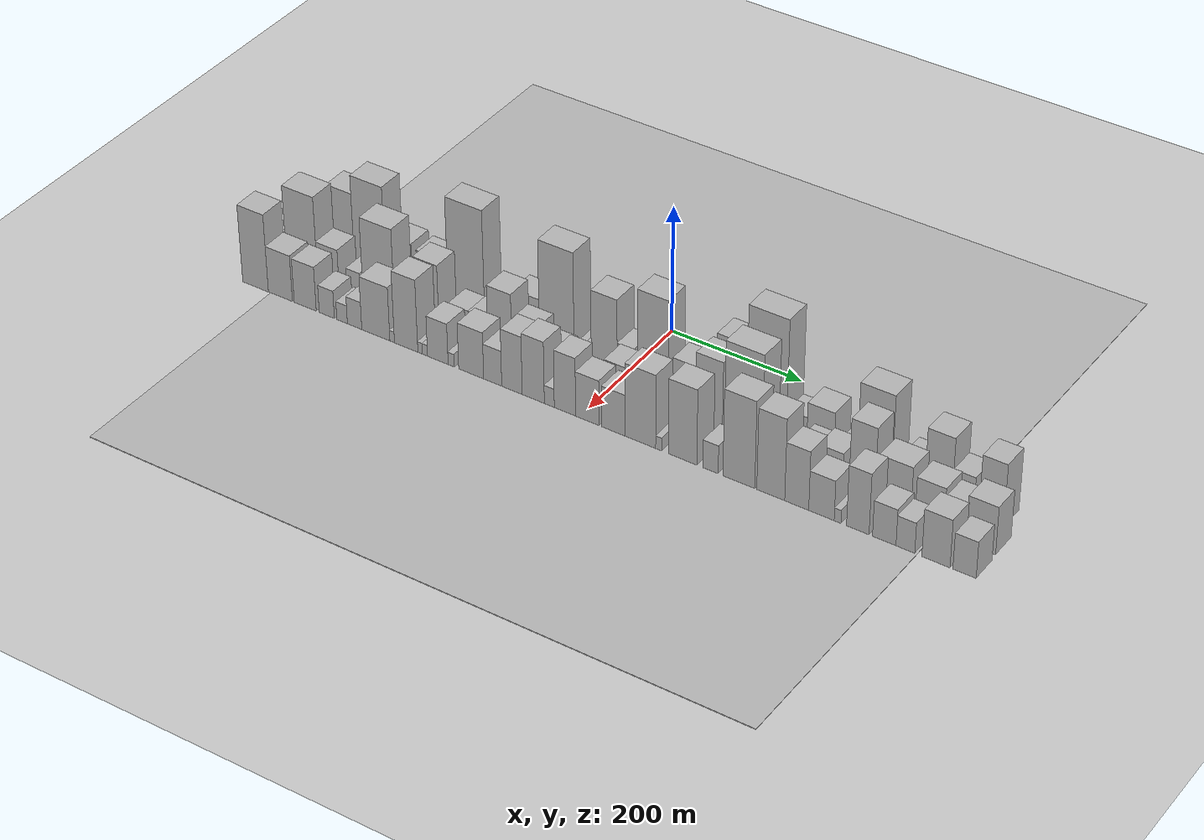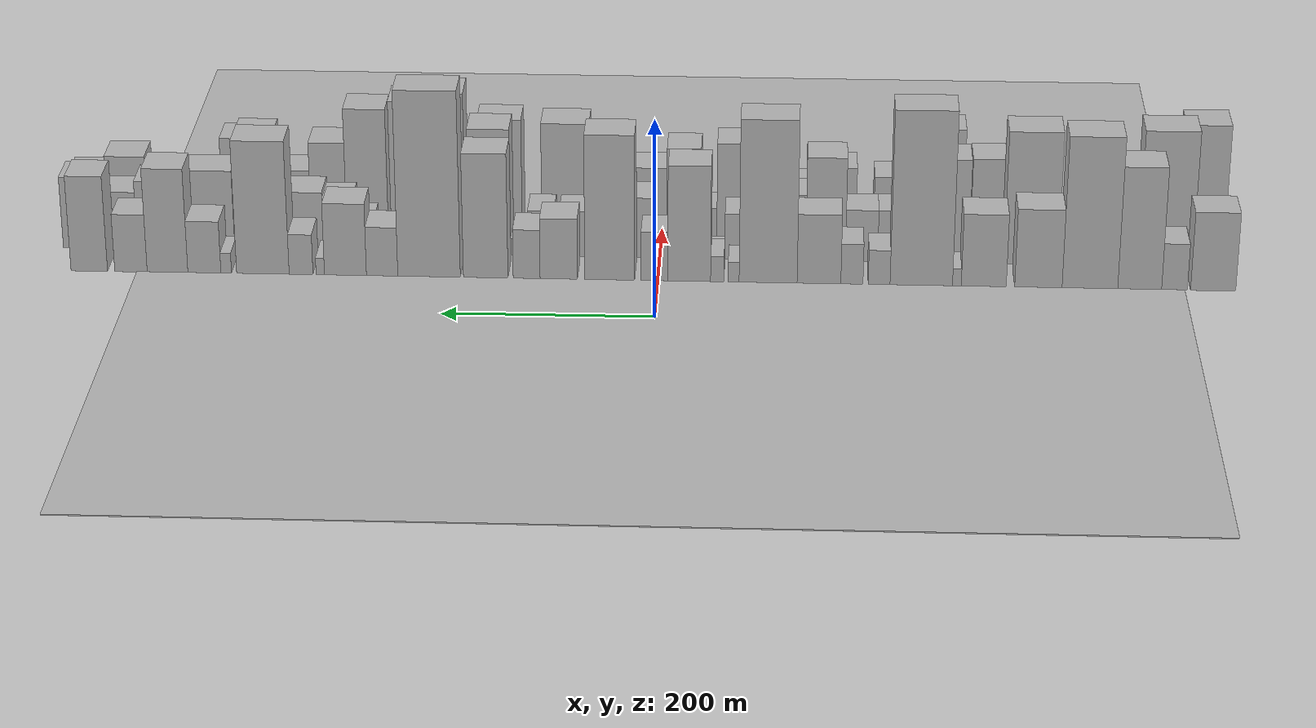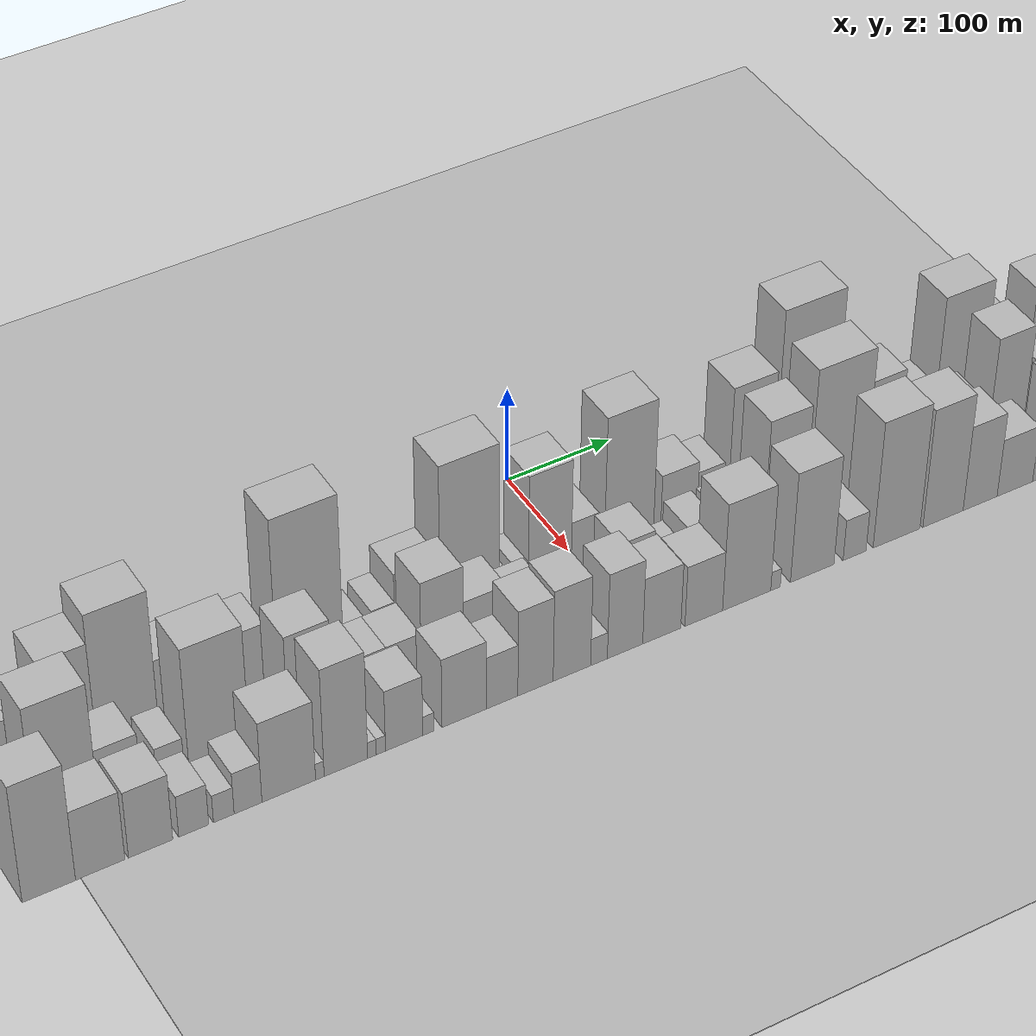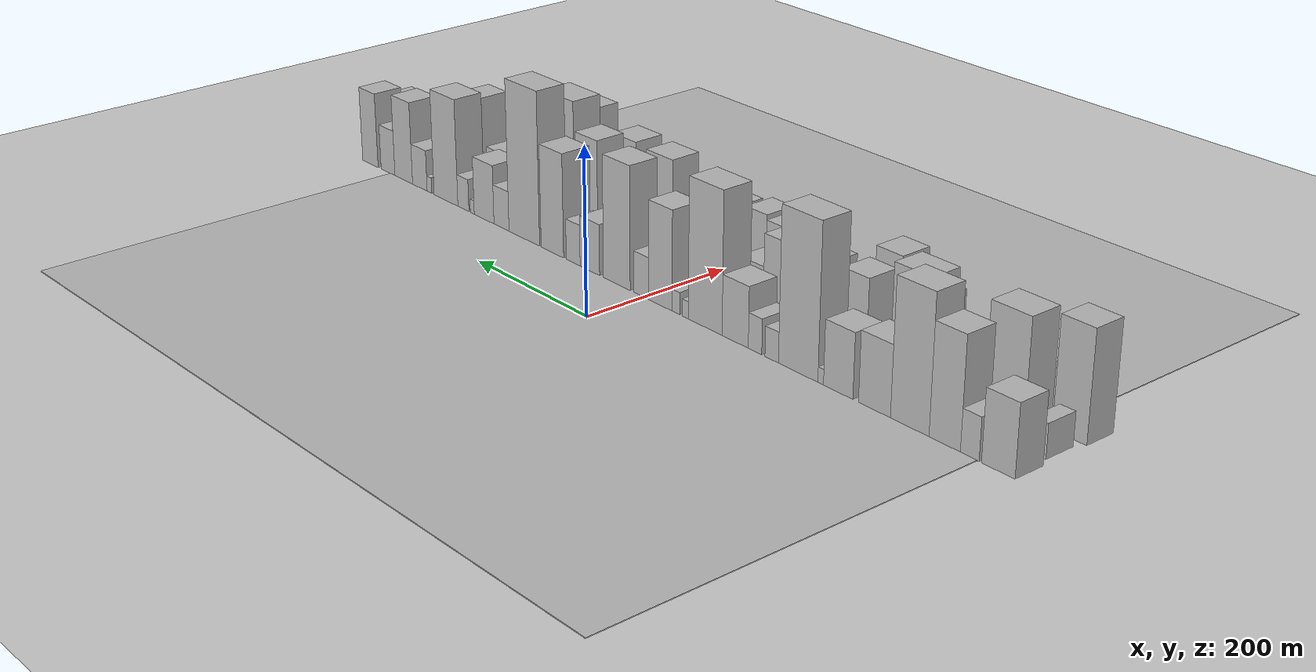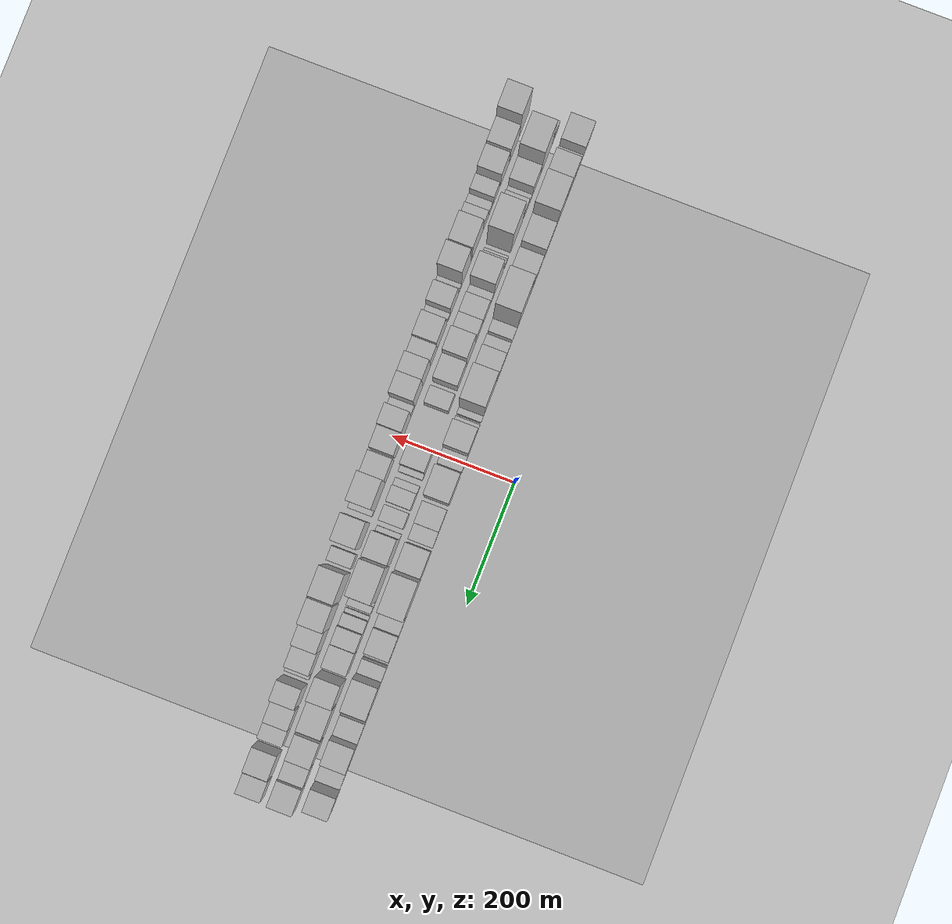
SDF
<?xml version="1.0" encoding="utf-8"?>

<sdf version="1.6">

   <world name="default">

      <gui fullscreen="0">

         <camera name="user_camera">

            <pose>-15 0 4.57585 0 0 0</pose>

            <view_controller>orbit</view_controller>

         </camera>

      </gui>

      <scene>

         <sky>

           <clouds>

             <speed>12</speed>

           </clouds>

         </sky>

         <ambient>0.4 0.4 0.4 1</ambient>

         <background>0.7 0.7 0.7 1</background>

         <shadows>1</shadows>

      </scene>

      <gravity>0 0 -9.8066</gravity>

      <magnetic_field>6e-06 2.3e-05 -4.2e-05</magnetic_field>

      <physics default="0" name="default_physics" type="ode">

         <ode>

            <solver>

               <type>quick</type>

               <iters>10</iters>

               <sor>1.0</sor>

               <use_dynamic_moi_rescaling>0</use_dynamic_moi_rescaling>

            </solver>

            <constraints>

               <cfm>0</cfm>

               <erp>0.2</erp>

               <contact_max_correcting_vel>100</contact_max_correcting_vel>

               <contact_surface_layer>0.001</contact_surface_layer>

            </constraints>

         </ode>

         <max_step_size>0.004</max_step_size>

         <real_time_factor>1</real_time_factor>

         <real_time_update_rate>250</real_time_update_rate>

      </physics>

      <light name="sun" type="directional">

         <cast_shadows>1</cast_shadows>

         <pose>0 0 10 0 0 0</pose>

         <diffuse>0.8 0.8 0.8 1</diffuse>

         <specular>0.2 0.2 0.2 1</specular>

         <attenuation>

            <range>1000</range>

            <constant>0.9</constant>

            <linear>0.01</linear>

            <quadratic>0.001</quadratic>

         </attenuation>

         <direction>-0.5 0.1 -0.9</direction>

      </light>

      <include>

         <name>ground_plane_1</name>

         <uri>model://HANNAS_ground_plane</uri>

         <pose>0 0 0  0 0 0</pose>

      </include>

      <include>

         <name>ground_plane_2</name>

         <uri>model://HANNAS_ground_plane</uri>

         <pose>100 0 0  0 0 0</pose>

      </include>

      <model name="building_1">

         <static>1</static>

         <pose frame="">100.0000 -526.6972 0 0.000000 0.000000 0.000000</pose>

         <link name="link">

            <pose frame="">0 0 40.50 0 0 0</pose>

            <collision name="collision">

               <geometry>

                  <box>

                     <size>40.0000 42.6056 81.0000</size>

                  </box>

               </geometry>

               <max_contacts>10</max_contacts>

               <surface>

                  <contact>

                     <ode/>

                  </contact>

                  <bounce/>

                  <friction>

                     <torsional>

                        <ode/>

                     </torsional>

                     <ode/>

                  </friction>

               </surface>

            </collision>

            <visual name="visual">

               <cast_shadows>0</cast_shadows>

               <geometry>

                  <box>

                     <size>40.0000 42.6056 81.0000</size>

                  </box>

               </geometry>

               <material>

                  <script>

                     <uri>model://HANNAS_wall/materials/scripts</uri>

                     <uri>model://HANNAS_wall/materials/textures</uri>

                     <name>vrc/HANNAS_wall</name>

                  </script>

               </material>

            </visual>

            <self_collide>0</self_collide>

            <enable_wind>0</enable_wind>

            <kinematic>0</kinematic>

         </link>

      </model>

      <model name="building_2">

         <static>1</static>

         <pose frame="">100.0000 -490.2368 0 0.000000 0.000000 0.000000</pose>

         <link name="link">

            <pose frame="">0 0 24.00 0 0 0</pose>

            <collision name="collision">

               <geometry>

                  <box>

                     <size>40.0000 24.3152 48.0000</size>

                  </box>

               </geometry>

               <max_contacts>10</max_contacts>

               <surface>

                  <contact>

                     <ode/>

                  </contact>

                  <bounce/>

                  <friction>

                     <torsional>

                        <ode/>

                     </torsional>

                     <ode/>

                  </friction>

               </surface>

            </collision>

            <visual name="visual">

               <cast_shadows>0</cast_shadows>

               <geometry>

                  <box>

                     <size>40.0000 24.3152 48.0000</size>

                  </box>

               </geometry>

               <material>

                  <script>

                     <uri>model://HANNAS_wall/materials/scripts</uri>

                     <uri>model://HANNAS_wall/materials/textures</uri>

                     <name>vrc/HANNAS_wall</name>

                  </script>

               </material>

            </visual>

            <self_collide>0</self_collide>

            <enable_wind>0</enable_wind>

            <kinematic>0</kinematic>

         </link>

      </model>

      <model name="building_3">

         <static>1</static>

         <pose frame="">100.0000 -457.3275 0 0.000000 0.000000 0.000000</pose>

         <link name="link">

            <pose frame="">0 0 63.00 0 0 0</pose>

            <collision name="collision">

               <geometry>

                  <box>

                     <size>40.0000 41.5033 126.0000</size>

                  </box>

               </geometry>

               <max_contacts>10</max_contacts>

               <surface>

                  <contact>

                     <ode/>

                  </contact>

                  <bounce/>

                  <friction>

                     <torsional>

                        <ode/>

                     </torsional>

                     <ode/>

                  </friction>

               </surface>

            </collision>

            <visual name="visual">

               <cast_shadows>0</cast_shadows>

               <geometry>

                  <box>

                     <size>40.0000 41.5033 126.0000</size>

                  </box>

               </geometry>

               <material>

                  <script>

                     <uri>model://HANNAS_wall/materials/scripts</uri>

                     <uri>model://HANNAS_wall/materials/textures</uri>

                     <name>vrc/HANNAS_wall</name>

                  </script>

               </material>

            </visual>

            <self_collide>0</self_collide>

            <enable_wind>0</enable_wind>

            <kinematic>0</kinematic>

         </link>

      </model>

      <model name="building_4">

         <static>1</static>

         <pose frame="">100.0000 -410.2595 0 0.000000 0.000000 0.000000</pose>

         <link name="link">

            <pose frame="">0 0 78.00 0 0 0</pose>

            <collision name="collision">

               <geometry>

                  <box>

                     <size>40.0000 52.6326 156.0000</size>

                  </box>

               </geometry>

               <max_contacts>10</max_contacts>

               <surface>

                  <contact>

                     <ode/>

                  </contact>

                  <bounce/>

                  <friction>

                     <torsional>

                        <ode/>

                     </torsional>

                     <ode/>

                  </friction>

               </surface>

            </collision>

            <visual name="visual">

               <cast_shadows>0</cast_shadows>

               <geometry>

                  <box>

                     <size>40.0000 52.6326 156.0000</size>

                  </box>

               </geometry>

               <material>

                  <script>

                     <uri>model://HANNAS_wall/materials/scripts</uri>

                     <uri>model://HANNAS_wall/materials/textures</uri>

                     <name>vrc/HANNAS_wall</name>

                  </script>

               </material>

            </visual>

            <self_collide>0</self_collide>

            <enable_wind>0</enable_wind>

            <kinematic>0</kinematic>

         </link>

      </model>

      <model name="building_5">

         <static>1</static>

         <pose frame="">100.0000 -361.5258 0 0.000000 0.000000 0.000000</pose>

         <link name="link">

            <pose frame="">0 0 40.50 0 0 0</pose>

            <collision name="collision">

               <geometry>

                  <box>

                     <size>40.0000 44.8348 81.0000</size>

                  </box>

               </geometry>

               <max_contacts>10</max_contacts>

               <surface>

                  <contact>

                     <ode/>

                  </contact>

                  <bounce/>

                  <friction>

                     <torsional>

                        <ode/>

                     </torsional>

                     <ode/>

                  </friction>

               </surface>

            </collision>

            <visual name="visual">

               <cast_shadows>0</cast_shadows>

               <geometry>

                  <box>

                     <size>40.0000 44.8348 81.0000</size>

                  </box>

               </geometry>

               <material>

                  <script>

                     <uri>model://HANNAS_wall/materials/scripts</uri>

                     <uri>model://HANNAS_wall/materials/textures</uri>

                     <name>vrc/HANNAS_wall</name>

                  </script>

               </material>

            </visual>

            <self_collide>0</self_collide>

            <enable_wind>0</enable_wind>

            <kinematic>0</kinematic>

         </link>

      </model>

      <model name="building_6">

         <static>1</static>

         <pose frame="">100.0000 -309.7806 0 0.000000 0.000000 0.000000</pose>

         <link name="link">

            <pose frame="">0 0 37.50 0 0 0</pose>

            <collision name="collision">

               <geometry>

                  <box>

                     <size>40.0000 42.6557 75.0000</size>

                  </box>

               </geometry>

               <max_contacts>10</max_contacts>

               <surface>

                  <contact>

                     <ode/>

                  </contact>

                  <bounce/>

                  <friction>

                     <torsional>

                        <ode/>

                     </torsional>

                     <ode/>

                  </friction>

               </surface>

            </collision>

            <visual name="visual">

               <cast_shadows>0</cast_shadows>

               <geometry>

                  <box>

                     <size>40.0000 42.6557 75.0000</size>

                  </box>

               </geometry>

               <material>

                  <script>

                     <uri>model://HANNAS_wall/materials/scripts</uri>

                     <uri>model://HANNAS_wall/materials/textures</uri>

                     <name>vrc/HANNAS_wall</name>

                  </script>

               </material>

            </visual>

            <self_collide>0</self_collide>

            <enable_wind>0</enable_wind>

            <kinematic>0</kinematic>

         </link>

      </model>

      <model name="building_7">

         <static>1</static>

         <pose frame="">100.0000 -284.2996 0 0.000000 0.000000 0.000000</pose>

         <link name="link">

            <pose frame="">0 0 9.00 0 0 0</pose>

            <collision name="collision">

               <geometry>

                  <box>

                     <size>40.0000 8.3063 18.0000</size>

                  </box>

               </geometry>

               <max_contacts>10</max_contacts>

               <surface>

                  <contact>

                     <ode/>

                  </contact>

                  <bounce/>

                  <friction>

                     <torsional>

                        <ode/>

                     </torsional>

                     <ode/>

                  </friction>

               </surface>

            </collision>

            <visual name="visual">

               <cast_shadows>0</cast_shadows>

               <geometry>

                  <box>

                     <size>40.0000 8.3063 18.0000</size>

                  </box>

               </geometry>

               <material>

                  <script>

                     <uri>model://HANNAS_wall/materials/scripts</uri>

                     <uri>model://HANNAS_wall/materials/textures</uri>

                     <name>vrc/HANNAS_wall</name>

                  </script>

               </material>

            </visual>

            <self_collide>0</self_collide>

            <enable_wind>0</enable_wind>

            <kinematic>0</kinematic>

         </link>

      </model>

      <model name="building_8">

         <static>1</static>

         <pose frame="">100.0000 -250.4863 0 0.000000 0.000000 0.000000</pose>

         <link name="link">

            <pose frame="">0 0 90.00 0 0 0</pose>

            <collision name="collision">

               <geometry>

                  <box>

                     <size>40.0000 59.3203 180.0000</size>

                  </box>

               </geometry>

               <max_contacts>10</max_contacts>

               <surface>

                  <contact>

                     <ode/>

                  </contact>

                  <bounce/>

                  <friction>

                     <torsional>

                        <ode/>

                     </torsional>

                     <ode/>

                  </friction>

               </surface>

            </collision>

            <visual name="visual">

               <cast_shadows>0</cast_shadows>

               <geometry>

                  <box>

                     <size>40.0000 59.3203 180.0000</size>

                  </box>

               </geometry>

               <material>

                  <script>

                     <uri>model://HANNAS_wall/materials/scripts</uri>

                     <uri>model://HANNAS_wall/materials/textures</uri>

                     <name>vrc/HANNAS_wall</name>

                  </script>

               </material>

            </visual>

            <self_collide>0</self_collide>

            <enable_wind>0</enable_wind>

            <kinematic>0</kinematic>

         </link>

      </model>

      <model name="building_9">

         <static>1</static>

         <pose frame="">100.0000 -210.4761 0 0.000000 0.000000 0.000000</pose>

         <link name="link">

            <pose frame="">0 0 18.00 0 0 0</pose>

            <collision name="collision">

               <geometry>

                  <box>

                     <size>40.0000 20.7000 36.0000</size>

                  </box>

               </geometry>

               <max_contacts>10</max_contacts>

               <surface>

                  <contact>

                     <ode/>

                  </contact>

                  <bounce/>

                  <friction>

                     <torsional>

                        <ode/>

                     </torsional>

                     <ode/>

                  </friction>

               </surface>

            </collision>

            <visual name="visual">

               <cast_shadows>0</cast_shadows>

               <geometry>

                  <box>

                     <size>40.0000 20.7000 36.0000</size>

                  </box>

               </geometry>

               <material>

                  <script>

                     <uri>model://HANNAS_wall/materials/scripts</uri>

                     <uri>model://HANNAS_wall/materials/textures</uri>

                     <name>vrc/HANNAS_wall</name>

                  </script>

               </material>

            </visual>

            <self_collide>0</self_collide>

            <enable_wind>0</enable_wind>

            <kinematic>0</kinematic>

         </link>

      </model>

      <model name="building_10">

         <static>1</static>

         <pose frame="">100.0000 -184.6078 0 0.000000 0.000000 0.000000</pose>

         <link name="link">

            <pose frame="">0 0 21.00 0 0 0</pose>

            <collision name="collision">

               <geometry>

                  <box>

                     <size>40.0000 21.0366 42.0000</size>

                  </box>

               </geometry>

               <max_contacts>10</max_contacts>

               <surface>

                  <contact>

                     <ode/>

                  </contact>

                  <bounce/>

                  <friction>

                     <torsional>

                        <ode/>

                     </torsional>

                     <ode/>

                  </friction>

               </surface>

            </collision>

            <visual name="visual">

               <cast_shadows>0</cast_shadows>

               <geometry>

                  <box>

                     <size>40.0000 21.0366 42.0000</size>

                  </box>

               </geometry>

               <material>

                  <script>

                     <uri>model://HANNAS_wall/materials/scripts</uri>

                     <uri>model://HANNAS_wall/materials/textures</uri>

                     <name>vrc/HANNAS_wall</name>

                  </script>

               </material>

            </visual>

            <self_collide>0</self_collide>

            <enable_wind>0</enable_wind>

            <kinematic>0</kinematic>

         </link>

      </model>

      <model name="building_11">

         <static>1</static>

         <pose frame="">100.0000 -153.2782 0 0.000000 0.000000 0.000000</pose>

         <link name="link">

            <pose frame="">0 0 36.00 0 0 0</pose>

            <collision name="collision">

               <geometry>

                  <box>

                     <size>40.0000 41.6225 72.0000</size>

                  </box>

               </geometry>

               <max_contacts>10</max_contacts>

               <surface>

                  <contact>

                     <ode/>

                  </contact>

                  <bounce/>

                  <friction>

                     <torsional>

                        <ode/>

                     </torsional>

                     <ode/>

                  </friction>

               </surface>

            </collision>

            <visual name="visual">

               <cast_shadows>0</cast_shadows>

               <geometry>

                  <box>

                     <size>40.0000 41.6225 72.0000</size>

                  </box>

               </geometry>

               <material>

                  <script>

                     <uri>model://HANNAS_wall/materials/scripts</uri>

                     <uri>model://HANNAS_wall/materials/textures</uri>

                     <name>vrc/HANNAS_wall</name>

                  </script>

               </material>

            </visual>

            <self_collide>0</self_collide>

            <enable_wind>0</enable_wind>

            <kinematic>0</kinematic>

         </link>

      </model>

      <model name="building_12">

         <static>1</static>

         <pose frame="">100.0000 -104.8603 0 0.000000 0.000000 0.000000</pose>

         <link name="link">

            <pose frame="">0 0 84.00 0 0 0</pose>

            <collision name="collision">

               <geometry>

                  <box>

                     <size>40.0000 55.2134 168.0000</size>

                  </box>

               </geometry>

               <max_contacts>10</max_contacts>

               <surface>

                  <contact>

                     <ode/>

                  </contact>

                  <bounce/>

                  <friction>

                     <torsional>

                        <ode/>

                     </torsional>

                     <ode/>

                  </friction>

               </surface>

            </collision>

            <visual name="visual">

               <cast_shadows>0</cast_shadows>

               <geometry>

                  <box>

                     <size>40.0000 55.2134 168.0000</size>

                  </box>

               </geometry>

               <material>

                  <script>

                     <uri>model://HANNAS_wall/materials/scripts</uri>

                     <uri>model://HANNAS_wall/materials/textures</uri>

                     <name>vrc/HANNAS_wall</name>

                  </script>

               </material>

            </visual>

            <self_collide>0</self_collide>

            <enable_wind>0</enable_wind>

            <kinematic>0</kinematic>

         </link>

      </model>

      <model name="building_13">

         <static>1</static>

         <pose frame="">100.0000 -72.0051 0 0.000000 0.000000 0.000000</pose>

         <link name="link">

            <pose frame="">0 0 10.50 0 0 0</pose>

            <collision name="collision">

               <geometry>

                  <box>

                     <size>40.0000 10.4969 21.0000</size>

                  </box>

               </geometry>

               <max_contacts>10</max_contacts>

               <surface>

                  <contact>

                     <ode/>

                  </contact>

                  <bounce/>

                  <friction>

                     <torsional>

                        <ode/>

                     </torsional>

                     <ode/>

                  </friction>

               </surface>

            </collision>

            <visual name="visual">

               <cast_shadows>0</cast_shadows>

               <geometry>

                  <box>

                     <size>40.0000 10.4969 21.0000</size>

                  </box>

               </geometry>

               <material>

                  <script>

                     <uri>model://HANNAS_wall/materials/scripts</uri>

                     <uri>model://HANNAS_wall/materials/textures</uri>

                     <name>vrc/HANNAS_wall</name>

                  </script>

               </material>

            </visual>

            <self_collide>0</self_collide>

            <enable_wind>0</enable_wind>

            <kinematic>0</kinematic>

         </link>

      </model>

      <model name="building_14">

         <static>1</static>

         <pose frame="">100.0000 -56.4145 0 0.000000 0.000000 0.000000</pose>

         <link name="link">

            <pose frame="">0 0 13.50 0 0 0</pose>

            <collision name="collision">

               <geometry>

                  <box>

                     <size>40.0000 12.6842 27.0000</size>

                  </box>

               </geometry>

               <max_contacts>10</max_contacts>

               <surface>

                  <contact>

                     <ode/>

                  </contact>

                  <bounce/>

                  <friction>

                     <torsional>

                        <ode/>

                     </torsional>

                     <ode/>

                  </friction>

               </surface>

            </collision>

            <visual name="visual">

               <cast_shadows>0</cast_shadows>

               <geometry>

                  <box>

                     <size>40.0000 12.6842 27.0000</size>

                  </box>

               </geometry>

               <material>

                  <script>

                     <uri>model://HANNAS_wall/materials/scripts</uri>

                     <uri>model://HANNAS_wall/materials/textures</uri>

                     <name>vrc/HANNAS_wall</name>

                  </script>

               </material>

            </visual>

            <self_collide>0</self_collide>

            <enable_wind>0</enable_wind>

            <kinematic>0</kinematic>

         </link>

      </model>

      <model name="building_15">

         <static>1</static>

         <pose frame="">100.0000 -29.7221 0 0.000000 0.000000 0.000000</pose>

         <link name="link">

            <pose frame="">0 0 60.00 0 0 0</pose>

            <collision name="collision">

               <geometry>

                  <box>

                     <size>40.0000 40.7008 120.0000</size>

                  </box>

               </geometry>

               <max_contacts>10</max_contacts>

               <surface>

                  <contact>

                     <ode/>

                  </contact>

                  <bounce/>

                  <friction>

                     <torsional>

                        <ode/>

                     </torsional>

                     <ode/>

                  </friction>

               </surface>

            </collision>

            <visual name="visual">

               <cast_shadows>0</cast_shadows>

               <geometry>

                  <box>

                     <size>40.0000 40.7008 120.0000</size>

                  </box>

               </geometry>

               <material>

                  <script>

                     <uri>model://HANNAS_wall/materials/scripts</uri>

                     <uri>model://HANNAS_wall/materials/textures</uri>

                     <name>vrc/HANNAS_wall</name>

                  </script>

               </material>

            </visual>

            <self_collide>0</self_collide>

            <enable_wind>0</enable_wind>

            <kinematic>0</kinematic>

         </link>

      </model>

      <model name="building_16">

         <static>1</static>

         <pose frame="">100.0000 3.4860 0 0.000000 0.000000 0.000000</pose>

         <link name="link">

            <pose frame="">0 0 25.50 0 0 0</pose>

            <collision name="collision">

               <geometry>

                  <box>

                     <size>40.0000 25.7153 51.0000</size>

                  </box>

               </geometry>

               <max_contacts>10</max_contacts>

               <surface>

                  <contact>

                     <ode/>

                  </contact>

                  <bounce/>

                  <friction>

                     <torsional>

                        <ode/>

                     </torsional>

                     <ode/>

                  </friction>

               </surface>

            </collision>

            <visual name="visual">

               <cast_shadows>0</cast_shadows>

               <geometry>

                  <box>

                     <size>40.0000 25.7153 51.0000</size>

                  </box>

               </geometry>

               <material>

                  <script>

                     <uri>model://HANNAS_wall/materials/scripts</uri>

                     <uri>model://HANNAS_wall/materials/textures</uri>

                     <name>vrc/HANNAS_wall</name>

                  </script>

               </material>

            </visual>

            <self_collide>0</self_collide>

            <enable_wind>0</enable_wind>

            <kinematic>0</kinematic>

         </link>

      </model>

      <model name="building_17">

         <static>1</static>

         <pose frame="">100.0000 46.1600 0 0.000000 0.000000 0.000000</pose>

         <link name="link">

            <pose frame="">0 0 75.00 0 0 0</pose>

            <collision name="collision">

               <geometry>

                  <box>

                     <size>40.0000 47.6328 150.0000</size>

                  </box>

               </geometry>

               <max_contacts>10</max_contacts>

               <surface>

                  <contact>

                     <ode/>

                  </contact>

                  <bounce/>

                  <friction>

                     <torsional>

                        <ode/>

                     </torsional>

                     <ode/>

                  </friction>

               </surface>

            </collision>

            <visual name="visual">

               <cast_shadows>0</cast_shadows>

               <geometry>

                  <box>

                     <size>40.0000 47.6328 150.0000</size>

                  </box>

               </geometry>

               <material>

                  <script>

                     <uri>model://HANNAS_wall/materials/scripts</uri>

                     <uri>model://HANNAS_wall/materials/textures</uri>

                     <name>vrc/HANNAS_wall</name>

                  </script>

               </material>

            </visual>

            <self_collide>0</self_collide>

            <enable_wind>0</enable_wind>

            <kinematic>0</kinematic>

         </link>

      </model>

      <model name="building_18">

         <static>1</static>

         <pose frame="">100.0000 94.8382 0 0.000000 0.000000 0.000000</pose>

         <link name="link">

            <pose frame="">0 0 31.50 0 0 0</pose>

            <collision name="collision">

               <geometry>

                  <box>

                     <size>40.0000 35.7236 63.0000</size>

                  </box>

               </geometry>

               <max_contacts>10</max_contacts>

               <surface>

                  <contact>

                     <ode/>

                  </contact>

                  <bounce/>

                  <friction>

                     <torsional>

                        <ode/>

                     </torsional>

                     <ode/>

                  </friction>

               </surface>

            </collision>

            <visual name="visual">

               <cast_shadows>0</cast_shadows>

               <geometry>

                  <box>

                     <size>40.0000 35.7236 63.0000</size>

                  </box>

               </geometry>

               <material>

                  <script>

                     <uri>model://HANNAS_wall/materials/scripts</uri>

                     <uri>model://HANNAS_wall/materials/textures</uri>

                     <name>vrc/HANNAS_wall</name>

                  </script>

               </material>

            </visual>

            <self_collide>0</self_collide>

            <enable_wind>0</enable_wind>

            <kinematic>0</kinematic>

         </link>

      </model>

      <model name="building_19">

         <static>1</static>

         <pose frame="">100.0000 125.5742 0 0.000000 0.000000 0.000000</pose>

         <link name="link">

            <pose frame="">0 0 25.50 0 0 0</pose>

            <collision name="collision">

               <geometry>

                  <box>

                     <size>40.0000 25.7485 51.0000</size>

                  </box>

               </geometry>

               <max_contacts>10</max_contacts>

               <surface>

                  <contact>

                     <ode/>

                  </contact>

                  <bounce/>

                  <friction>

                     <torsional>

                        <ode/>

                     </torsional>

                     <ode/>

                  </friction>

               </surface>

            </collision>

            <visual name="visual">

               <cast_shadows>0</cast_shadows>

               <geometry>

                  <box>

                     <size>40.0000 25.7485 51.0000</size>

                  </box>

               </geometry>

               <material>

                  <script>

                     <uri>model://HANNAS_wall/materials/scripts</uri>

                     <uri>model://HANNAS_wall/materials/textures</uri>

                     <name>vrc/HANNAS_wall</name>

                  </script>

               </material>

            </visual>

            <self_collide>0</self_collide>

            <enable_wind>0</enable_wind>

            <kinematic>0</kinematic>

         </link>

      </model>

      <model name="building_20">

         <static>1</static>

         <pose frame="">100.0000 164.7653 0 0.000000 0.000000 0.000000</pose>

         <link name="link">

            <pose frame="">0 0 64.50 0 0 0</pose>

            <collision name="collision">

               <geometry>

                  <box>

                     <size>40.0000 42.6338 129.0000</size>

                  </box>

               </geometry>

               <max_contacts>10</max_contacts>

               <surface>

                  <contact>

                     <ode/>

                  </contact>

                  <bounce/>

                  <friction>

                     <torsional>

                        <ode/>

                     </torsional>

                     <ode/>

                  </friction>

               </surface>

            </collision>

            <visual name="visual">

               <cast_shadows>0</cast_shadows>

               <geometry>

                  <box>

                     <size>40.0000 42.6338 129.0000</size>

                  </box>

               </geometry>

               <material>

                  <script>

                     <uri>model://HANNAS_wall/materials/scripts</uri>

                     <uri>model://HANNAS_wall/materials/textures</uri>

                     <name>vrc/HANNAS_wall</name>

                  </script>

               </material>

            </visual>

            <self_collide>0</self_collide>

            <enable_wind>0</enable_wind>

            <kinematic>0</kinematic>

         </link>

      </model>

      <model name="building_21">

         <static>1</static>

         <pose frame="">100.0000 219.0663 0 0.000000 0.000000 0.000000</pose>

         <link name="link">

            <pose frame="">0 0 96.00 0 0 0</pose>

            <collision name="collision">

               <geometry>

                  <box>

                     <size>40.0000 59.9683 192.0000</size>

                  </box>

               </geometry>

               <max_contacts>10</max_contacts>

               <surface>

                  <contact>

                     <ode/>

                  </contact>

                  <bounce/>

                  <friction>

                     <torsional>

                        <ode/>

                     </torsional>

                     <ode/>

                  </friction>

               </surface>

            </collision>

            <visual name="visual">

               <cast_shadows>0</cast_shadows>

               <geometry>

                  <box>

                     <size>40.0000 59.9683 192.0000</size>

                  </box>

               </geometry>

               <material>

                  <script>

                     <uri>model://HANNAS_wall/materials/scripts</uri>

                     <uri>model://HANNAS_wall/materials/textures</uri>

                     <name>vrc/HANNAS_wall</name>

                  </script>

               </material>

            </visual>

            <self_collide>0</self_collide>

            <enable_wind>0</enable_wind>

            <kinematic>0</kinematic>

         </link>

      </model>

      <model name="building_22">

         <static>1</static>

         <pose frame="">100.0000 264.0907 0 0.000000 0.000000 0.000000</pose>

         <link name="link">

            <pose frame="">0 0 25.50 0 0 0</pose>

            <collision name="collision">

               <geometry>

                  <box>

                     <size>40.0000 30.0804 51.0000</size>

                  </box>

               </geometry>

               <max_contacts>10</max_contacts>

               <surface>

                  <contact>

                     <ode/>

                  </contact>

                  <bounce/>

                  <friction>

                     <torsional>

                        <ode/>

                     </torsional>

                     <ode/>

                  </friction>

               </surface>

            </collision>

            <visual name="visual">

               <cast_shadows>0</cast_shadows>

               <geometry>

                  <box>

                     <size>40.0000 30.0804 51.0000</size>

                  </box>

               </geometry>

               <material>

                  <script>

                     <uri>model://HANNAS_wall/materials/scripts</uri>

                     <uri>model://HANNAS_wall/materials/textures</uri>

                     <name>vrc/HANNAS_wall</name>

                  </script>

               </material>

            </visual>

            <self_collide>0</self_collide>

            <enable_wind>0</enable_wind>

            <kinematic>0</kinematic>

         </link>

      </model>

      <model name="building_23">

         <static>1</static>

         <pose frame="">100.0000 299.2750 0 0.000000 0.000000 0.000000</pose>

         <link name="link">

            <pose frame="">0 0 37.50 0 0 0</pose>

            <collision name="collision">

               <geometry>

                  <box>

                     <size>40.0000 40.2883 75.0000</size>

                  </box>

               </geometry>

               <max_contacts>10</max_contacts>

               <surface>

                  <contact>

                     <ode/>

                  </contact>

                  <bounce/>

                  <friction>

                     <torsional>

                        <ode/>

                     </torsional>

                     <ode/>

                  </friction>

               </surface>

            </collision>

            <visual name="visual">

               <cast_shadows>0</cast_shadows>

               <geometry>

                  <box>

                     <size>40.0000 40.2883 75.0000</size>

                  </box>

               </geometry>

               <material>

                  <script>

                     <uri>model://HANNAS_wall/materials/scripts</uri>

                     <uri>model://HANNAS_wall/materials/textures</uri>

                     <name>vrc/HANNAS_wall</name>

                  </script>

               </material>

            </visual>

            <self_collide>0</self_collide>

            <enable_wind>0</enable_wind>

            <kinematic>0</kinematic>

         </link>

      </model>

      <model name="building_24">

         <static>1</static>

         <pose frame="">100.0000 323.4559 0 0.000000 0.000000 0.000000</pose>

         <link name="link">

            <pose frame="">0 0 9.00 0 0 0</pose>

            <collision name="collision">

               <geometry>

                  <box>

                     <size>40.0000 8.0735 18.0000</size>

                  </box>

               </geometry>

               <max_contacts>10</max_contacts>

               <surface>

                  <contact>

                     <ode/>

                  </contact>

                  <bounce/>

                  <friction>

                     <torsional>

                        <ode/>

                     </torsional>

                     <ode/>

                  </friction>

               </surface>

            </collision>

            <visual name="visual">

               <cast_shadows>0</cast_shadows>

               <geometry>

                  <box>

                     <size>40.0000 8.0735 18.0000</size>

                  </box>

               </geometry>

               <material>

                  <script>

                     <uri>model://HANNAS_wall/materials/scripts</uri>

                     <uri>model://HANNAS_wall/materials/textures</uri>

                     <name>vrc/HANNAS_wall</name>

                  </script>

               </material>

            </visual>

            <self_collide>0</self_collide>

            <enable_wind>0</enable_wind>

            <kinematic>0</kinematic>

         </link>

      </model>

      <model name="building_25">

         <static>1</static>

         <pose frame="">100.0000 341.9341 0 0.000000 0.000000 0.000000</pose>

         <link name="link">

            <pose frame="">0 0 21.00 0 0 0</pose>

            <collision name="collision">

               <geometry>

                  <box>

                     <size>40.0000 22.8829 42.0000</size>

                  </box>

               </geometry>

               <max_contacts>10</max_contacts>

               <surface>

                  <contact>

                     <ode/>

                  </contact>

                  <bounce/>

                  <friction>

                     <torsional>

                        <ode/>

                     </torsional>

                     <ode/>

                  </friction>

               </surface>

            </collision>

            <visual name="visual">

               <cast_shadows>0</cast_shadows>

               <geometry>

                  <box>

                     <size>40.0000 22.8829 42.0000</size>

                  </box>

               </geometry>

               <material>

                  <script>

                     <uri>model://HANNAS_wall/materials/scripts</uri>

                     <uri>model://HANNAS_wall/materials/textures</uri>

                     <name>vrc/HANNAS_wall</name>

                  </script>

               </material>

            </visual>

            <self_collide>0</self_collide>

            <enable_wind>0</enable_wind>

            <kinematic>0</kinematic>

         </link>

      </model>

      <model name="building_26">

         <static>1</static>

         <pose frame="">100.0000 378.6242 0 0.000000 0.000000 0.000000</pose>

         <link name="link">

            <pose frame="">0 0 69.00 0 0 0</pose>

            <collision name="collision">

               <geometry>

                  <box>

                     <size>40.0000 50.4972 138.0000</size>

                  </box>

               </geometry>

               <max_contacts>10</max_contacts>

               <surface>

                  <contact>

                     <ode/>

                  </contact>

                  <bounce/>

                  <friction>

                     <torsional>

                        <ode/>

                     </torsional>

                     <ode/>

                  </friction>

               </surface>

            </collision>

            <visual name="visual">

               <cast_shadows>0</cast_shadows>

               <geometry>

                  <box>

                     <size>40.0000 50.4972 138.0000</size>

                  </box>

               </geometry>

               <material>

                  <script>

                     <uri>model://HANNAS_wall/materials/scripts</uri>

                     <uri>model://HANNAS_wall/materials/textures</uri>

                     <name>vrc/HANNAS_wall</name>

                  </script>

               </material>

            </visual>

            <self_collide>0</self_collide>

            <enable_wind>0</enable_wind>

            <kinematic>0</kinematic>

         </link>

      </model>

      <model name="building_27">

         <static>1</static>

         <pose frame="">100.0000 413.9518 0 0.000000 0.000000 0.000000</pose>

         <link name="link">

            <pose frame="">0 0 10.50 0 0 0</pose>

            <collision name="collision">

               <geometry>

                  <box>

                     <size>40.0000 10.1581 21.0000</size>

                  </box>

               </geometry>

               <max_contacts>10</max_contacts>

               <surface>

                  <contact>

                     <ode/>

                  </contact>

                  <bounce/>

                  <friction>

                     <torsional>

                        <ode/>

                     </torsional>

                     <ode/>

                  </friction>

               </surface>

            </collision>

            <visual name="visual">

               <cast_shadows>0</cast_shadows>

               <geometry>

                  <box>

                     <size>40.0000 10.1581 21.0000</size>

                  </box>

               </geometry>

               <material>

                  <script>

                     <uri>model://HANNAS_wall/materials/scripts</uri>

                     <uri>model://HANNAS_wall/materials/textures</uri>

                     <name>vrc/HANNAS_wall</name>

                  </script>

               </material>

            </visual>

            <self_collide>0</self_collide>

            <enable_wind>0</enable_wind>

            <kinematic>0</kinematic>

         </link>

      </model>

      <model name="building_28">

         <static>1</static>

         <pose frame="">100.0000 434.9588 0 0.000000 0.000000 0.000000</pose>

         <link name="link">

            <pose frame="">0 0 27.00 0 0 0</pose>

            <collision name="collision">

               <geometry>

                  <box>

                     <size>40.0000 31.8559 54.0000</size>

                  </box>

               </geometry>

               <max_contacts>10</max_contacts>

               <surface>

                  <contact>

                     <ode/>

                  </contact>

                  <bounce/>

                  <friction>

                     <torsional>

                        <ode/>

                     </torsional>

                     <ode/>

                  </friction>

               </surface>

            </collision>

            <visual name="visual">

               <cast_shadows>0</cast_shadows>

               <geometry>

                  <box>

                     <size>40.0000 31.8559 54.0000</size>

                  </box>

               </geometry>

               <material>

                  <script>

                     <uri>model://HANNAS_wall/materials/scripts</uri>

                     <uri>model://HANNAS_wall/materials/textures</uri>

                     <name>vrc/HANNAS_wall</name>

                  </script>

               </material>

            </visual>

            <self_collide>0</self_collide>

            <enable_wind>0</enable_wind>

            <kinematic>0</kinematic>

         </link>

      </model>

      <model name="building_29">

         <static>1</static>

         <pose frame="">100.0000 470.4755 0 0.000000 0.000000 0.000000</pose>

         <link name="link">

            <pose frame="">0 0 54.00 0 0 0</pose>

            <collision name="collision">

               <geometry>

                  <box>

                     <size>40.0000 39.1775 108.0000</size>

                  </box>

               </geometry>

               <max_contacts>10</max_contacts>

               <surface>

                  <contact>

                     <ode/>

                  </contact>

                  <bounce/>

                  <friction>

                     <torsional>

                        <ode/>

                     </torsional>

                     <ode/>

                  </friction>

               </surface>

            </collision>

            <visual name="visual">

               <cast_shadows>0</cast_shadows>

               <geometry>

                  <box>

                     <size>40.0000 39.1775 108.0000</size>

                  </box>

               </geometry>

               <material>

                  <script>

                     <uri>model://HANNAS_wall/materials/scripts</uri>

                     <uri>model://HANNAS_wall/materials/textures</uri>

                     <name>vrc/HANNAS_wall</name>

                  </script>

               </material>

            </visual>

            <self_collide>0</self_collide>

            <enable_wind>0</enable_wind>

            <kinematic>0</kinematic>

         </link>

      </model>

      <model name="building_30">

         <static>1</static>

         <pose frame="">100.0000 505.7085 0 0.000000 0.000000 0.000000</pose>

         <link name="link">

            <pose frame="">0 0 30.00 0 0 0</pose>

            <collision name="collision">

               <geometry>

                  <box>

                     <size>40.0000 31.2883 60.0000</size>

                  </box>

               </geometry>

               <max_contacts>10</max_contacts>

               <surface>

                  <contact>

                     <ode/>

                  </contact>

                  <bounce/>

                  <friction>

                     <torsional>

                        <ode/>

                     </torsional>

                     <ode/>

                  </friction>

               </surface>

            </collision>

            <visual name="visual">

               <cast_shadows>0</cast_shadows>

               <geometry>

                  <box>

                     <size>40.0000 31.2883 60.0000</size>

                  </box>

               </geometry>

               <material>

                  <script>

                     <uri>model://HANNAS_wall/materials/scripts</uri>

                     <uri>model://HANNAS_wall/materials/textures</uri>

                     <name>vrc/HANNAS_wall</name>

                  </script>

               </material>

            </visual>

            <self_collide>0</self_collide>

            <enable_wind>0</enable_wind>

            <kinematic>0</kinematic>

         </link>

      </model>

      <model name="building_31">

         <static>1</static>

         <pose frame="">100.0000 545.9888 0 0.000000 0.000000 0.000000</pose>

         <link name="link">

            <pose frame="">0 0 49.50 0 0 0</pose>

            <collision name="collision">

               <geometry>

                  <box>

                     <size>40.0000 35.2724 99.0000</size>

                  </box>

               </geometry>

               <max_contacts>10</max_contacts>

               <surface>

                  <contact>

                     <ode/>

                  </contact>

                  <bounce/>

                  <friction>

                     <torsional>

                        <ode/>

                     </torsional>

                     <ode/>

                  </friction>

               </surface>

            </collision>

            <visual name="visual">

               <cast_shadows>0</cast_shadows>

               <geometry>

                  <box>

                     <size>40.0000 35.2724 99.0000</size>

                  </box>

               </geometry>

               <material>

                  <script>

                     <uri>model://HANNAS_wall/materials/scripts</uri>

                     <uri>model://HANNAS_wall/materials/textures</uri>

                     <name>vrc/HANNAS_wall</name>

                  </script>

               </material>

            </visual>

            <self_collide>0</self_collide>

            <enable_wind>0</enable_wind>

            <kinematic>0</kinematic>

         </link>

      </model>

      <model name="building_32">

         <static>1</static>

         <pose frame="">152.0000 -530.9299 0 0.000000 0.000000 0.000000</pose>

         <link name="link">

            <pose frame="">0 0 19.50 0 0 0</pose>

            <collision name="collision">

               <geometry>

                  <box>

                     <size>40.0000 20.1402 39.0000</size>

                  </box>

               </geometry>

               <max_contacts>10</max_contacts>

               <surface>

                  <contact>

                     <ode/>

                  </contact>

                  <bounce/>

                  <friction>

                     <torsional>

                        <ode/>

                     </torsional>

                     <ode/>

                  </friction>

               </surface>

            </collision>

            <visual name="visual">

               <cast_shadows>0</cast_shadows>

               <geometry>

                  <box>

                     <size>40.0000 20.1402 39.0000</size>

                  </box>

               </geometry>

               <material>

                  <script>

                     <uri>model://HANNAS_wall/materials/scripts</uri>

                     <uri>model://HANNAS_wall/materials/textures</uri>

                     <name>vrc/HANNAS_wall</name>

                  </script>

               </material>

            </visual>

            <self_collide>0</self_collide>

            <enable_wind>0</enable_wind>

            <kinematic>0</kinematic>

         </link>

      </model>

      <model name="building_33">

         <static>1</static>

         <pose frame="">152.0000 -516.4928 0 0.000000 0.000000 0.000000</pose>

         <link name="link">

            <pose frame="">0 0 9.00 0 0 0</pose>

            <collision name="collision">

               <geometry>

                  <box>

                     <size>40.0000 8.7341 18.0000</size>

                  </box>

               </geometry>

               <max_contacts>10</max_contacts>

               <surface>

                  <contact>

                     <ode/>

                  </contact>

                  <bounce/>

                  <friction>

                     <torsional>

                        <ode/>

                     </torsional>

                     <ode/>

                  </friction>

               </surface>

            </collision>

            <visual name="visual">

               <cast_shadows>0</cast_shadows>

               <geometry>

                  <box>

                     <size>40.0000 8.7341 18.0000</size>

                  </box>

               </geometry>

               <material>

                  <script>

                     <uri>model://HANNAS_wall/materials/scripts</uri>

                     <uri>model://HANNAS_wall/materials/textures</uri>

                     <name>vrc/HANNAS_wall</name>

                  </script>

               </material>

            </visual>

            <self_collide>0</self_collide>

            <enable_wind>0</enable_wind>

            <kinematic>0</kinematic>

         </link>

      </model>

      <model name="building_34">

         <static>1</static>

         <pose frame="">152.0000 -486.0516 0 0.000000 0.000000 0.000000</pose>

         <link name="link">

            <pose frame="">0 0 70.50 0 0 0</pose>

            <collision name="collision">

               <geometry>

                  <box>

                     <size>40.0000 52.1482 141.0000</size>

                  </box>

               </geometry>

               <max_contacts>10</max_contacts>

               <surface>

                  <contact>

                     <ode/>

                  </contact>

                  <bounce/>

                  <friction>

                     <torsional>

                        <ode/>

                     </torsional>

                     <ode/>

                  </friction>

               </surface>

            </collision>

            <visual name="visual">

               <cast_shadows>0</cast_shadows>

               <geometry>

                  <box>

                     <size>40.0000 52.1482 141.0000</size>

                  </box>

               </geometry>

               <material>

                  <script>

                     <uri>model://HANNAS_wall/materials/scripts</uri>

                     <uri>model://HANNAS_wall/materials/textures</uri>

                     <name>vrc/HANNAS_wall</name>

                  </script>

               </material>

            </visual>

            <self_collide>0</self_collide>

            <enable_wind>0</enable_wind>

            <kinematic>0</kinematic>

         </link>

      </model>

      <model name="building_35">

         <static>1</static>

         <pose frame="">152.0000 -441.9299 0 0.000000 0.000000 0.000000</pose>

         <link name="link">

            <pose frame="">0 0 34.50 0 0 0</pose>

            <collision name="collision">

               <geometry>

                  <box>

                     <size>40.0000 36.0953 69.0000</size>

                  </box>

               </geometry>

               <max_contacts>10</max_contacts>

               <surface>

                  <contact>

                     <ode/>

                  </contact>

                  <bounce/>

                  <friction>

                     <torsional>

                        <ode/>

                     </torsional>

                     <ode/>

                  </friction>

               </surface>

            </collision>

            <visual name="visual">

               <cast_shadows>0</cast_shadows>

               <geometry>

                  <box>

                     <size>40.0000 36.0953 69.0000</size>

                  </box>

               </geometry>

               <material>

                  <script>

                     <uri>model://HANNAS_wall/materials/scripts</uri>

                     <uri>model://HANNAS_wall/materials/textures</uri>

                     <name>vrc/HANNAS_wall</name>

                  </script>

               </material>

            </visual>

            <self_collide>0</self_collide>

            <enable_wind>0</enable_wind>

            <kinematic>0</kinematic>

         </link>

      </model>

      <model name="building_36">

         <static>1</static>

         <pose frame="">152.0000 -419.4189 0 0.000000 0.000000 0.000000</pose>

         <link name="link">

            <pose frame="">0 0 10.50 0 0 0</pose>

            <collision name="collision">

               <geometry>

                  <box>

                     <size>40.0000 8.9266 21.0000</size>

                  </box>

               </geometry>

               <max_contacts>10</max_contacts>

               <surface>

                  <contact>

                     <ode/>

                  </contact>

                  <bounce/>

                  <friction>

                     <torsional>

                        <ode/>

                     </torsional>

                     <ode/>

                  </friction>

               </surface>

            </collision>

            <visual name="visual">

               <cast_shadows>0</cast_shadows>

               <geometry>

                  <box>

                     <size>40.0000 8.9266 21.0000</size>

                  </box>

               </geometry>

               <material>

                  <script>

                     <uri>model://HANNAS_wall/materials/scripts</uri>

                     <uri>model://HANNAS_wall/materials/textures</uri>

                     <name>vrc/HANNAS_wall</name>

                  </script>

               </material>

            </visual>

            <self_collide>0</self_collide>

            <enable_wind>0</enable_wind>

            <kinematic>0</kinematic>

         </link>

      </model>

      <model name="building_37">

         <static>1</static>

         <pose frame="">152.0000 -399.2062 0 0.000000 0.000000 0.000000</pose>

         <link name="link">

            <pose frame="">0 0 22.50 0 0 0</pose>

            <collision name="collision">

               <geometry>

                  <box>

                     <size>40.0000 23.4989 45.0000</size>

                  </box>

               </geometry>

               <max_contacts>10</max_contacts>

               <surface>

                  <contact>

                     <ode/>

                  </contact>

                  <bounce/>

                  <friction>

                     <torsional>

                        <ode/>

                     </torsional>

                     <ode/>

                  </friction>

               </surface>

            </collision>

            <visual name="visual">

               <cast_shadows>0</cast_shadows>

               <geometry>

                  <box>

                     <size>40.0000 23.4989 45.0000</size>

                  </box>

               </geometry>

               <material>

                  <script>

                     <uri>model://HANNAS_wall/materials/scripts</uri>

                     <uri>model://HANNAS_wall/materials/textures</uri>

                     <name>vrc/HANNAS_wall</name>

                  </script>

               </material>

            </visual>

            <self_collide>0</self_collide>

            <enable_wind>0</enable_wind>

            <kinematic>0</kinematic>

         </link>

      </model>

      <model name="building_38">

         <static>1</static>

         <pose frame="">152.0000 -357.3748 0 0.000000 0.000000 0.000000</pose>

         <link name="link">

            <pose frame="">0 0 69.00 0 0 0</pose>

            <collision name="collision">

               <geometry>

                  <box>

                     <size>40.0000 52.1639 138.0000</size>

                  </box>

               </geometry>

               <max_contacts>10</max_contacts>

               <surface>

                  <contact>

                     <ode/>

                  </contact>

                  <bounce/>

                  <friction>

                     <torsional>

                        <ode/>

                     </torsional>

                     <ode/>

                  </friction>

               </surface>

            </collision>

            <visual name="visual">

               <cast_shadows>0</cast_shadows>

               <geometry>

                  <box>

                     <size>40.0000 52.1639 138.0000</size>

                  </box>

               </geometry>

               <material>

                  <script>

                     <uri>model://HANNAS_wall/materials/scripts</uri>

                     <uri>model://HANNAS_wall/materials/textures</uri>

                     <name>vrc/HANNAS_wall</name>

                  </script>

               </material>

            </visual>

            <self_collide>0</self_collide>

            <enable_wind>0</enable_wind>

            <kinematic>0</kinematic>

         </link>

      </model>

      <model name="building_39">

         <static>1</static>

         <pose frame="">152.0000 -319.0195 0 0.000000 0.000000 0.000000</pose>

         <link name="link">

            <pose frame="">0 0 7.50 0 0 0</pose>

            <collision name="collision">

               <geometry>

                  <box>

                     <size>40.0000 6.5467 15.0000</size>

                  </box>

               </geometry>

               <max_contacts>10</max_contacts>

               <surface>

                  <contact>

                     <ode/>

                  </contact>

                  <bounce/>

                  <friction>

                     <torsional>

                        <ode/>

                     </torsional>

                     <ode/>

                  </friction>

               </surface>

            </collision>

            <visual name="visual">

               <cast_shadows>0</cast_shadows>

               <geometry>

                  <box>

                     <size>40.0000 6.5467 15.0000</size>

                  </box>

               </geometry>

               <material>

                  <script>

                     <uri>model://HANNAS_wall/materials/scripts</uri>

                     <uri>model://HANNAS_wall/materials/textures</uri>

                     <name>vrc/HANNAS_wall</name>

                  </script>

               </material>

            </visual>

            <self_collide>0</self_collide>

            <enable_wind>0</enable_wind>

            <kinematic>0</kinematic>

         </link>

      </model>

      <model name="building_40">

         <static>1</static>

         <pose frame="">152.0000 -309.1297 0 0.000000 0.000000 0.000000</pose>

         <link name="link">

            <pose frame="">0 0 13.50 0 0 0</pose>

            <collision name="collision">

               <geometry>

                  <box>

                     <size>40.0000 13.2327 27.0000</size>

                  </box>

               </geometry>

               <max_contacts>10</max_contacts>

               <surface>

                  <contact>

                     <ode/>

                  </contact>

                  <bounce/>

                  <friction>

                     <torsional>

                        <ode/>

                     </torsional>

                     <ode/>

                  </friction>

               </surface>

            </collision>

            <visual name="visual">

               <cast_shadows>0</cast_shadows>

               <geometry>

                  <box>

                     <size>40.0000 13.2327 27.0000</size>

                  </box>

               </geometry>

               <material>

                  <script>

                     <uri>model://HANNAS_wall/materials/scripts</uri>

                     <uri>model://HANNAS_wall/materials/textures</uri>

                     <name>vrc/HANNAS_wall</name>

                  </script>

               </material>

            </visual>

            <self_collide>0</self_collide>

            <enable_wind>0</enable_wind>

            <kinematic>0</kinematic>

         </link>

      </model>

      <model name="building_41">

         <static>1</static>

         <pose frame="">152.0000 -277.9080 0 0.000000 0.000000 0.000000</pose>

         <link name="link">

            <pose frame="">0 0 54.00 0 0 0</pose>

            <collision name="collision">

               <geometry>

                  <box>

                     <size>40.0000 39.2107 108.0000</size>

                  </box>

               </geometry>

               <max_contacts>10</max_contacts>

               <surface>

                  <contact>

                     <ode/>

                  </contact>

                  <bounce/>

                  <friction>

                     <torsional>

                        <ode/>

                     </torsional>

                     <ode/>

                  </friction>

               </surface>

            </collision>

            <visual name="visual">

               <cast_shadows>0</cast_shadows>

               <geometry>

                  <box>

                     <size>40.0000 39.2107 108.0000</size>

                  </box>

               </geometry>

               <material>

                  <script>

                     <uri>model://HANNAS_wall/materials/scripts</uri>

                     <uri>model://HANNAS_wall/materials/textures</uri>

                     <name>vrc/HANNAS_wall</name>

                  </script>

               </material>

            </visual>

            <self_collide>0</self_collide>

            <enable_wind>0</enable_wind>

            <kinematic>0</kinematic>

         </link>

      </model>

      <model name="building_42">

         <static>1</static>

         <pose frame="">152.0000 -250.2431 0 0.000000 0.000000 0.000000</pose>

         <link name="link">

            <pose frame="">0 0 15.00 0 0 0</pose>

            <collision name="collision">

               <geometry>

                  <box>

                     <size>40.0000 16.1190 30.0000</size>

                  </box>

               </geometry>

               <max_contacts>10</max_contacts>

               <surface>

                  <contact>

                     <ode/>

                  </contact>

                  <bounce/>

                  <friction>

                     <torsional>

                        <ode/>

                     </torsional>

                     <ode/>

                  </friction>

               </surface>

            </collision>

            <visual name="visual">

               <cast_shadows>0</cast_shadows>

               <geometry>

                  <box>

                     <size>40.0000 16.1190 30.0000</size>

                  </box>

               </geometry>

               <material>

                  <script>

                     <uri>model://HANNAS_wall/materials/scripts</uri>

                     <uri>model://HANNAS_wall/materials/textures</uri>

                     <name>vrc/HANNAS_wall</name>

                  </script>

               </material>

            </visual>

            <self_collide>0</self_collide>

            <enable_wind>0</enable_wind>

            <kinematic>0</kinematic>

         </link>

      </model>

      <model name="building_43">

         <static>1</static>

         <pose frame="">152.0000 -226.0797 0 0.000000 0.000000 0.000000</pose>

         <link name="link">

            <pose frame="">0 0 27.00 0 0 0</pose>

            <collision name="collision">

               <geometry>

                  <box>

                     <size>40.0000 32.2078 54.0000</size>

                  </box>

               </geometry>

               <max_contacts>10</max_contacts>

               <surface>

                  <contact>

                     <ode/>

                  </contact>

                  <bounce/>

                  <friction>

                     <torsional>

                        <ode/>

                     </torsional>

                     <ode/>

                  </friction>

               </surface>

            </collision>

            <visual name="visual">

               <cast_shadows>0</cast_shadows>

               <geometry>

                  <box>

                     <size>40.0000 32.2078 54.0000</size>

                  </box>

               </geometry>

               <material>

                  <script>

                     <uri>model://HANNAS_wall/materials/scripts</uri>

                     <uri>model://HANNAS_wall/materials/textures</uri>

                     <name>vrc/HANNAS_wall</name>

                  </script>

               </material>

            </visual>

            <self_collide>0</self_collide>

            <enable_wind>0</enable_wind>

            <kinematic>0</kinematic>

         </link>

      </model>

      <model name="building_44">

         <static>1</static>

         <pose frame="">152.0000 -194.4050 0 0.000000 0.000000 0.000000</pose>

         <link name="link">

            <pose frame="">0 0 27.00 0 0 0</pose>

            <collision name="collision">

               <geometry>

                  <box>

                     <size>40.0000 31.1416 54.0000</size>

                  </box>

               </geometry>

               <max_contacts>10</max_contacts>

               <surface>

                  <contact>

                     <ode/>

                  </contact>

                  <bounce/>

                  <friction>

                     <torsional>

                        <ode/>

                     </torsional>

                     <ode/>

                  </friction>

               </surface>

            </collision>

            <visual name="visual">

               <cast_shadows>0</cast_shadows>

               <geometry>

                  <box>

                     <size>40.0000 31.1416 54.0000</size>

                  </box>

               </geometry>

               <material>

                  <script>

                     <uri>model://HANNAS_wall/materials/scripts</uri>

                     <uri>model://HANNAS_wall/materials/textures</uri>

                     <name>vrc/HANNAS_wall</name>

                  </script>

               </material>

            </visual>

            <self_collide>0</self_collide>

            <enable_wind>0</enable_wind>

            <kinematic>0</kinematic>

         </link>

      </model>

      <model name="building_45">

         <static>1</static>

         <pose frame="">152.0000 -159.6991 0 0.000000 0.000000 0.000000</pose>

         <link name="link">

            <pose frame="">0 0 54.00 0 0 0</pose>

            <collision name="collision">

               <geometry>

                  <box>

                     <size>40.0000 38.2703 108.0000</size>

                  </box>

               </geometry>

               <max_contacts>10</max_contacts>

               <surface>

                  <contact>

                     <ode/>

                  </contact>

                  <bounce/>

                  <friction>

                     <torsional>

                        <ode/>

                     </torsional>

                     <ode/>

                  </friction>

               </surface>

            </collision>

            <visual name="visual">

               <cast_shadows>0</cast_shadows>

               <geometry>

                  <box>

                     <size>40.0000 38.2703 108.0000</size>

                  </box>

               </geometry>

               <material>

                  <script>

                     <uri>model://HANNAS_wall/materials/scripts</uri>

                     <uri>model://HANNAS_wall/materials/textures</uri>

                     <name>vrc/HANNAS_wall</name>

                  </script>

               </material>

            </visual>

            <self_collide>0</self_collide>

            <enable_wind>0</enable_wind>

            <kinematic>0</kinematic>

         </link>

      </model>

      <model name="building_46">

         <static>1</static>

         <pose frame="">152.0000 -120.7294 0 0.000000 0.000000 0.000000</pose>

         <link name="link">

            <pose frame="">0 0 34.50 0 0 0</pose>

            <collision name="collision">

               <geometry>

                  <box>

                     <size>40.0000 39.6692 69.0000</size>

                  </box>

               </geometry>

               <max_contacts>10</max_contacts>

               <surface>

                  <contact>

                     <ode/>

                  </contact>

                  <bounce/>

                  <friction>

                     <torsional>

                        <ode/>

                     </torsional>

                     <ode/>

                  </friction>

               </surface>

            </collision>

            <visual name="visual">

               <cast_shadows>0</cast_shadows>

               <geometry>

                  <box>

                     <size>40.0000 39.6692 69.0000</size>

                  </box>

               </geometry>

               <material>

                  <script>

                     <uri>model://HANNAS_wall/materials/scripts</uri>

                     <uri>model://HANNAS_wall/materials/textures</uri>

                     <name>vrc/HANNAS_wall</name>

                  </script>

               </material>

            </visual>

            <self_collide>0</self_collide>

            <enable_wind>0</enable_wind>

            <kinematic>0</kinematic>

         </link>

      </model>

      <model name="building_47">

         <static>1</static>

         <pose frame="">152.0000 -76.7160 0 0.000000 0.000000 0.000000</pose>

         <link name="link">

            <pose frame="">0 0 24.00 0 0 0</pose>

            <collision name="collision">

               <geometry>

                  <box>

                     <size>40.0000 28.3577 48.0000</size>

                  </box>

               </geometry>

               <max_contacts>10</max_contacts>

               <surface>

                  <contact>

                     <ode/>

                  </contact>

                  <bounce/>

                  <friction>

                     <torsional>

                        <ode/>

                     </torsional>

                     <ode/>

                  </friction>

               </surface>

            </collision>

            <visual name="visual">

               <cast_shadows>0</cast_shadows>

               <geometry>

                  <box>

                     <size>40.0000 28.3577 48.0000</size>

                  </box>

               </geometry>

               <material>

                  <script>

                     <uri>model://HANNAS_wall/materials/scripts</uri>

                     <uri>model://HANNAS_wall/materials/textures</uri>

                     <name>vrc/HANNAS_wall</name>

                  </script>

               </material>

            </visual>

            <self_collide>0</self_collide>

            <enable_wind>0</enable_wind>

            <kinematic>0</kinematic>

         </link>

      </model>

      <model name="building_48">

         <static>1</static>

         <pose frame="">152.0000 21.1618 0 0.000000 0.000000 0.000000</pose>

         <link name="link">

            <pose frame="">0 0 31.50 0 0 0</pose>

            <collision name="collision">

               <geometry>

                  <box>

                     <size>40.0000 33.1326 63.0000</size>

                  </box>

               </geometry>

               <max_contacts>10</max_contacts>

               <surface>

                  <contact>

                     <ode/>

                  </contact>

                  <bounce/>

                  <friction>

                     <torsional>

                        <ode/>

                     </torsional>

                     <ode/>

                  </friction>

               </surface>

            </collision>

            <visual name="visual">

               <cast_shadows>0</cast_shadows>

               <geometry>

                  <box>

                     <size>40.0000 33.1326 63.0000</size>

                  </box>

               </geometry>

               <material>

                  <script>

                     <uri>model://HANNAS_wall/materials/scripts</uri>

                     <uri>model://HANNAS_wall/materials/textures</uri>

                     <name>vrc/HANNAS_wall</name>

                  </script>

               </material>

            </visual>

            <self_collide>0</self_collide>

            <enable_wind>0</enable_wind>

            <kinematic>0</kinematic>

         </link>

      </model>

      <model name="building_49">

         <static>1</static>

         <pose frame="">152.0000 42.7620 0 0.000000 0.000000 0.000000</pose>

         <link name="link">

            <pose frame="">0 0 10.50 0 0 0</pose>

            <collision name="collision">

               <geometry>

                  <box>

                     <size>40.0000 10.0676 21.0000</size>

                  </box>

               </geometry>

               <max_contacts>10</max_contacts>

               <surface>

                  <contact>

                     <ode/>

                  </contact>

                  <bounce/>

                  <friction>

                     <torsional>

                        <ode/>

                     </torsional>

                     <ode/>

                  </friction>

               </surface>

            </collision>

            <visual name="visual">

               <cast_shadows>0</cast_shadows>

               <geometry>

                  <box>

                     <size>40.0000 10.0676 21.0000</size>

                  </box>

               </geometry>

               <material>

                  <script>

                     <uri>model://HANNAS_wall/materials/scripts</uri>

                     <uri>model://HANNAS_wall/materials/textures</uri>

                     <name>vrc/HANNAS_wall</name>

                  </script>

               </material>

            </visual>

            <self_collide>0</self_collide>

            <enable_wind>0</enable_wind>

            <kinematic>0</kinematic>

         </link>

      </model>

      <model name="building_50">

         <static>1</static>

         <pose frame="">152.0000 64.2689 0 0.000000 0.000000 0.000000</pose>

         <link name="link">

            <pose frame="">0 0 13.50 0 0 0</pose>

            <collision name="collision">

               <geometry>

                  <box>

                     <size>40.0000 12.9463 27.0000</size>

                  </box>

               </geometry>

               <max_contacts>10</max_contacts>

               <surface>

                  <contact>

                     <ode/>

                  </contact>

                  <bounce/>

                  <friction>

                     <torsional>

                        <ode/>

                     </torsional>

                     <ode/>

                  </friction>

               </surface>

            </collision>

            <visual name="visual">

               <cast_shadows>0</cast_shadows>

               <geometry>

                  <box>

                     <size>40.0000 12.9463 27.0000</size>

                  </box>

               </geometry>

               <material>

                  <script>

                     <uri>model://HANNAS_wall/materials/scripts</uri>

                     <uri>model://HANNAS_wall/materials/textures</uri>

                     <name>vrc/HANNAS_wall</name>

                  </script>

               </material>

            </visual>

            <self_collide>0</self_collide>

            <enable_wind>0</enable_wind>

            <kinematic>0</kinematic>

         </link>

      </model>

      <model name="building_51">

         <static>1</static>

         <pose frame="">152.0000 84.0770 0 0.000000 0.000000 0.000000</pose>

         <link name="link">

            <pose frame="">0 0 24.00 0 0 0</pose>

            <collision name="collision">

               <geometry>

                  <box>

                     <size>40.0000 26.6699 48.0000</size>

                  </box>

               </geometry>

               <max_contacts>10</max_contacts>

               <surface>

                  <contact>

                     <ode/>

                  </contact>

                  <bounce/>

                  <friction>

                     <torsional>

                        <ode/>

                     </torsional>

                     <ode/>

                  </friction>

               </surface>

            </collision>

            <visual name="visual">

               <cast_shadows>0</cast_shadows>

               <geometry>

                  <box>

                     <size>40.0000 26.6699 48.0000</size>

                  </box>

               </geometry>

               <material>

                  <script>

                     <uri>model://HANNAS_wall/materials/scripts</uri>

                     <uri>model://HANNAS_wall/materials/textures</uri>

                     <name>vrc/HANNAS_wall</name>

                  </script>

               </material>

            </visual>

            <self_collide>0</self_collide>

            <enable_wind>0</enable_wind>

            <kinematic>0</kinematic>

         </link>

      </model>

      <model name="building_52">

         <static>1</static>

         <pose frame="">152.0000 115.1577 0 0.000000 0.000000 0.000000</pose>

         <link name="link">

            <pose frame="">0 0 24.00 0 0 0</pose>

            <collision name="collision">

               <geometry>

                  <box>

                     <size>40.0000 25.4915 48.0000</size>

                  </box>

               </geometry>

               <max_contacts>10</max_contacts>

               <surface>

                  <contact>

                     <ode/>

                  </contact>

                  <bounce/>

                  <friction>

                     <torsional>

                        <ode/>

                     </torsional>

                     <ode/>

                  </friction>

               </surface>

            </collision>

            <visual name="visual">

               <cast_shadows>0</cast_shadows>

               <geometry>

                  <box>

                     <size>40.0000 25.4915 48.0000</size>

                  </box>

               </geometry>

               <material>

                  <script>

                     <uri>model://HANNAS_wall/materials/scripts</uri>

                     <uri>model://HANNAS_wall/materials/textures</uri>

                     <name>vrc/HANNAS_wall</name>

                  </script>

               </material>

            </visual>

            <self_collide>0</self_collide>

            <enable_wind>0</enable_wind>

            <kinematic>0</kinematic>

         </link>

      </model>

      <model name="building_53">

         <static>1</static>

         <pose frame="">152.0000 140.2911 0 0.000000 0.000000 0.000000</pose>

         <link name="link">

            <pose frame="">0 0 9.00 0 0 0</pose>

            <collision name="collision">

               <geometry>

                  <box>

                     <size>40.0000 8.7753 18.0000</size>

                  </box>

               </geometry>

               <max_contacts>10</max_contacts>

               <surface>

                  <contact>

                     <ode/>

                  </contact>

                  <bounce/>

                  <friction>

                     <torsional>

                        <ode/>

                     </torsional>

                     <ode/>

                  </friction>

               </surface>

            </collision>

            <visual name="visual">

               <cast_shadows>0</cast_shadows>

               <geometry>

                  <box>

                     <size>40.0000 8.7753 18.0000</size>

                  </box>

               </geometry>

               <material>

                  <script>

                     <uri>model://HANNAS_wall/materials/scripts</uri>

                     <uri>model://HANNAS_wall/materials/textures</uri>

                     <name>vrc/HANNAS_wall</name>

                  </script>

               </material>

            </visual>

            <self_collide>0</self_collide>

            <enable_wind>0</enable_wind>

            <kinematic>0</kinematic>

         </link>

      </model>

      <model name="building_54">

         <static>1</static>

         <pose frame="">152.0000 164.9378 0 0.000000 0.000000 0.000000</pose>

         <link name="link">

            <pose frame="">0 0 66.00 0 0 0</pose>

            <collision name="collision">

               <geometry>

                  <box>

                     <size>40.0000 40.5182 132.0000</size>

                  </box>

               </geometry>

               <max_contacts>10</max_contacts>

               <surface>

                  <contact>

                     <ode/>

                  </contact>

                  <bounce/>

                  <friction>

                     <torsional>

                        <ode/>

                     </torsional>

                     <ode/>

                  </friction>

               </surface>

            </collision>

            <visual name="visual">

               <cast_shadows>0</cast_shadows>

               <geometry>

                  <box>

                     <size>40.0000 40.5182 132.0000</size>

                  </box>

               </geometry>

               <material>

                  <script>

                     <uri>model://HANNAS_wall/materials/scripts</uri>

                     <uri>model://HANNAS_wall/materials/textures</uri>

                     <name>vrc/HANNAS_wall</name>

                  </script>

               </material>

            </visual>

            <self_collide>0</self_collide>

            <enable_wind>0</enable_wind>

            <kinematic>0</kinematic>

         </link>

      </model>

      <model name="building_55">

         <static>1</static>

         <pose frame="">152.0000 216.6067 0 0.000000 0.000000 0.000000</pose>

         <link name="link">

            <pose frame="">0 0 84.00 0 0 0</pose>

            <collision name="collision">

               <geometry>

                  <box>

                     <size>40.0000 56.8195 168.0000</size>

                  </box>

               </geometry>

               <max_contacts>10</max_contacts>

               <surface>

                  <contact>

                     <ode/>

                  </contact>

                  <bounce/>

                  <friction>

                     <torsional>

                        <ode/>

                     </torsional>

                     <ode/>

                  </friction>

               </surface>

            </collision>

            <visual name="visual">

               <cast_shadows>0</cast_shadows>

               <geometry>

                  <box>

                     <size>40.0000 56.8195 168.0000</size>

                  </box>

               </geometry>

               <material>

                  <script>

                     <uri>model://HANNAS_wall/materials/scripts</uri>

                     <uri>model://HANNAS_wall/materials/textures</uri>

                     <name>vrc/HANNAS_wall</name>

                  </script>

               </material>

            </visual>

            <self_collide>0</self_collide>

            <enable_wind>0</enable_wind>

            <kinematic>0</kinematic>

         </link>

      </model>

      <model name="building_56">

         <static>1</static>

         <pose frame="">152.0000 249.3709 0 0.000000 0.000000 0.000000</pose>

         <link name="link">

            <pose frame="">0 0 9.00 0 0 0</pose>

            <collision name="collision">

               <geometry>

                  <box>

                     <size>40.0000 8.7090 18.0000</size>

                  </box>

               </geometry>

               <max_contacts>10</max_contacts>

               <surface>

                  <contact>

                     <ode/>

                  </contact>

                  <bounce/>

                  <friction>

                     <torsional>

                        <ode/>

                     </torsional>

                     <ode/>

                  </friction>

               </surface>

            </collision>

            <visual name="visual">

               <cast_shadows>0</cast_shadows>

               <geometry>

                  <box>

                     <size>40.0000 8.7090 18.0000</size>

                  </box>

               </geometry>

               <material>

                  <script>

                     <uri>model://HANNAS_wall/materials/scripts</uri>

                     <uri>model://HANNAS_wall/materials/textures</uri>

                     <name>vrc/HANNAS_wall</name>

                  </script>

               </material>

            </visual>

            <self_collide>0</self_collide>

            <enable_wind>0</enable_wind>

            <kinematic>0</kinematic>

         </link>

      </model>

      <model name="building_57">

         <static>1</static>

         <pose frame="">152.0000 259.5027 0 0.000000 0.000000 0.000000</pose>

         <link name="link">

            <pose frame="">0 0 13.50 0 0 0</pose>

            <collision name="collision">

               <geometry>

                  <box>

                     <size>40.0000 11.5546 27.0000</size>

                  </box>

               </geometry>

               <max_contacts>10</max_contacts>

               <surface>

                  <contact>

                     <ode/>

                  </contact>

                  <bounce/>

                  <friction>

                     <torsional>

                        <ode/>

                     </torsional>

                     <ode/>

                  </friction>

               </surface>

            </collision>

            <visual name="visual">

               <cast_shadows>0</cast_shadows>

               <geometry>

                  <box>

                     <size>40.0000 11.5546 27.0000</size>

                  </box>

               </geometry>

               <material>

                  <script>

                     <uri>model://HANNAS_wall/materials/scripts</uri>

                     <uri>model://HANNAS_wall/materials/textures</uri>

                     <name>vrc/HANNAS_wall</name>

                  </script>

               </material>

            </visual>

            <self_collide>0</self_collide>

            <enable_wind>0</enable_wind>

            <kinematic>0</kinematic>

         </link>

      </model>

      <model name="building_58">

         <static>1</static>

         <pose frame="">152.0000 272.9842 0 0.000000 0.000000 0.000000</pose>

         <link name="link">

            <pose frame="">0 0 7.50 0 0 0</pose>

            <collision name="collision">

               <geometry>

                  <box>

                     <size>40.0000 7.4084 15.0000</size>

                  </box>

               </geometry>

               <max_contacts>10</max_contacts>

               <surface>

                  <contact>

                     <ode/>

                  </contact>

                  <bounce/>

                  <friction>

                     <torsional>

                        <ode/>

                     </torsional>

                     <ode/>

                  </friction>

               </surface>

            </collision>

            <visual name="visual">

               <cast_shadows>0</cast_shadows>

               <geometry>

                  <box>

                     <size>40.0000 7.4084 15.0000</size>

                  </box>

               </geometry>

               <material>

                  <script>

                     <uri>model://HANNAS_wall/materials/scripts</uri>

                     <uri>model://HANNAS_wall/materials/textures</uri>

                     <name>vrc/HANNAS_wall</name>

                  </script>

               </material>

            </visual>

            <self_collide>0</self_collide>

            <enable_wind>0</enable_wind>

            <kinematic>0</kinematic>

         </link>

      </model>

      <model name="building_59">

         <static>1</static>

         <pose frame="">152.0000 286.9562 0 0.000000 0.000000 0.000000</pose>

         <link name="link">

            <pose frame="">0 0 18.00 0 0 0</pose>

            <collision name="collision">

               <geometry>

                  <box>

                     <size>40.0000 20.5356 36.0000</size>

                  </box>

               </geometry>

               <max_contacts>10</max_contacts>

               <surface>

                  <contact>

                     <ode/>

                  </contact>

                  <bounce/>

                  <friction>

                     <torsional>

                        <ode/>

                     </torsional>

                     <ode/>

                  </friction>

               </surface>

            </collision>

            <visual name="visual">

               <cast_shadows>0</cast_shadows>

               <geometry>

                  <box>

                     <size>40.0000 20.5356 36.0000</size>

                  </box>

               </geometry>

               <material>

                  <script>

                     <uri>model://HANNAS_wall/materials/scripts</uri>

                     <uri>model://HANNAS_wall/materials/textures</uri>

                     <name>vrc/HANNAS_wall</name>

                  </script>

               </material>

            </visual>

            <self_collide>0</self_collide>

            <enable_wind>0</enable_wind>

            <kinematic>0</kinematic>

         </link>

      </model>

      <model name="building_60">

         <static>1</static>

         <pose frame="">152.0000 311.8248 0 0.000000 0.000000 0.000000</pose>

         <link name="link">

            <pose frame="">0 0 28.50 0 0 0</pose>

            <collision name="collision">

               <geometry>

                  <box>

                     <size>40.0000 29.2014 57.0000</size>

                  </box>

               </geometry>

               <max_contacts>10</max_contacts>

               <surface>

                  <contact>

                     <ode/>

                  </contact>

                  <bounce/>

                  <friction>

                     <torsional>

                        <ode/>

                     </torsional>

                     <ode/>

                  </friction>

               </surface>

            </collision>

            <visual name="visual">

               <cast_shadows>0</cast_shadows>

               <geometry>

                  <box>

                     <size>40.0000 29.2014 57.0000</size>

                  </box>

               </geometry>

               <material>

                  <script>

                     <uri>model://HANNAS_wall/materials/scripts</uri>

                     <uri>model://HANNAS_wall/materials/textures</uri>

                     <name>vrc/HANNAS_wall</name>

                  </script>

               </material>

            </visual>

            <self_collide>0</self_collide>

            <enable_wind>0</enable_wind>

            <kinematic>0</kinematic>

         </link>

      </model>

      <model name="building_61">

         <static>1</static>

         <pose frame="">152.0000 344.5707 0 0.000000 0.000000 0.000000</pose>

         <link name="link">

            <pose frame="">0 0 31.50 0 0 0</pose>

            <collision name="collision">

               <geometry>

                  <box>

                     <size>40.0000 36.2905 63.0000</size>

                  </box>

               </geometry>

               <max_contacts>10</max_contacts>

               <surface>

                  <contact>

                     <ode/>

                  </contact>

                  <bounce/>

                  <friction>

                     <torsional>

                        <ode/>

                     </torsional>

                     <ode/>

                  </friction>

               </surface>

            </collision>

            <visual name="visual">

               <cast_shadows>0</cast_shadows>

               <geometry>

                  <box>

                     <size>40.0000 36.2905 63.0000</size>

                  </box>

               </geometry>

               <material>

                  <script>

                     <uri>model://HANNAS_wall/materials/scripts</uri>

                     <uri>model://HANNAS_wall/materials/textures</uri>

                     <name>vrc/HANNAS_wall</name>

                  </script>

               </material>

            </visual>

            <self_collide>0</self_collide>

            <enable_wind>0</enable_wind>

            <kinematic>0</kinematic>

         </link>

      </model>

      <model name="building_62">

         <static>1</static>

         <pose frame="">152.0000 390.3841 0 0.000000 0.000000 0.000000</pose>

         <link name="link">

            <pose frame="">0 0 61.50 0 0 0</pose>

            <collision name="collision">

               <geometry>

                  <box>

                     <size>40.0000 37.3363 123.0000</size>

                  </box>

               </geometry>

               <max_contacts>10</max_contacts>

               <surface>

                  <contact>

                     <ode/>

                  </contact>

                  <bounce/>

                  <friction>

                     <torsional>

                        <ode/>

                     </torsional>

                     <ode/>

                  </friction>

               </surface>

            </collision>

            <visual name="visual">

               <cast_shadows>0</cast_shadows>

               <geometry>

                  <box>

                     <size>40.0000 37.3363 123.0000</size>

                  </box>

               </geometry>

               <material>

                  <script>

                     <uri>model://HANNAS_wall/materials/scripts</uri>

                     <uri>model://HANNAS_wall/materials/textures</uri>

                     <name>vrc/HANNAS_wall</name>

                  </script>

               </material>

            </visual>

            <self_collide>0</self_collide>

            <enable_wind>0</enable_wind>

            <kinematic>0</kinematic>

         </link>

      </model>

      <model name="building_63">

         <static>1</static>

         <pose frame="">152.0000 436.9797 0 0.000000 0.000000 0.000000</pose>

         <link name="link">

            <pose frame="">0 0 42.00 0 0 0</pose>

            <collision name="collision">

               <geometry>

                  <box>

                     <size>40.0000 47.8548 84.0000</size>

                  </box>

               </geometry>

               <max_contacts>10</max_contacts>

               <surface>

                  <contact>

                     <ode/>

                  </contact>

                  <bounce/>

                  <friction>

                     <torsional>

                        <ode/>

                     </torsional>

                     <ode/>

                  </friction>

               </surface>

            </collision>

            <visual name="visual">

               <cast_shadows>0</cast_shadows>

               <geometry>

                  <box>

                     <size>40.0000 47.8548 84.0000</size>

                  </box>

               </geometry>

               <material>

                  <script>

                     <uri>model://HANNAS_wall/materials/scripts</uri>

                     <uri>model://HANNAS_wall/materials/textures</uri>

                     <name>vrc/HANNAS_wall</name>

                  </script>

               </material>

            </visual>

            <self_collide>0</self_collide>

            <enable_wind>0</enable_wind>

            <kinematic>0</kinematic>

         </link>

      </model>

      <model name="building_64">

         <static>1</static>

         <pose frame="">152.0000 487.4974 0 0.000000 0.000000 0.000000</pose>

         <link name="link">

            <pose frame="">0 0 36.00 0 0 0</pose>

            <collision name="collision">

               <geometry>

                  <box>

                     <size>40.0000 41.1808 72.0000</size>

                  </box>

               </geometry>

               <max_contacts>10</max_contacts>

               <surface>

                  <contact>

                     <ode/>

                  </contact>

                  <bounce/>

                  <friction>

                     <torsional>

                        <ode/>

                     </torsional>

                     <ode/>

                  </friction>

               </surface>

            </collision>

            <visual name="visual">

               <cast_shadows>0</cast_shadows>

               <geometry>

                  <box>

                     <size>40.0000 41.1808 72.0000</size>

                  </box>

               </geometry>

               <material>

                  <script>

                     <uri>model://HANNAS_wall/materials/scripts</uri>

                     <uri>model://HANNAS_wall/materials/textures</uri>

                     <name>vrc/HANNAS_wall</name>

                  </script>

               </material>

            </visual>

            <self_collide>0</self_collide>

            <enable_wind>0</enable_wind>

            <kinematic>0</kinematic>

         </link>

      </model>

      <model name="building_65">

         <static>1</static>

         <pose frame="">152.0000 523.5968 0 0.000000 0.000000 0.000000</pose>

         <link name="link">

            <pose frame="">0 0 30.00 0 0 0</pose>

            <collision name="collision">

               <geometry>

                  <box>

                     <size>40.0000 31.0179 60.0000</size>

                  </box>

               </geometry>

               <max_contacts>10</max_contacts>

               <surface>

                  <contact>

                     <ode/>

                  </contact>

                  <bounce/>

                  <friction>

                     <torsional>

                        <ode/>

                     </torsional>

                     <ode/>

                  </friction>

               </surface>

            </collision>

            <visual name="visual">

               <cast_shadows>0</cast_shadows>

               <geometry>

                  <box>

                     <size>40.0000 31.0179 60.0000</size>

                  </box>

               </geometry>

               <material>

                  <script>

                     <uri>model://HANNAS_wall/materials/scripts</uri>

                     <uri>model://HANNAS_wall/materials/textures</uri>

                     <name>vrc/HANNAS_wall</name>

                  </script>

               </material>

            </visual>

            <self_collide>0</self_collide>

            <enable_wind>0</enable_wind>

            <kinematic>0</kinematic>

         </link>

      </model>

      <model name="building_66">

         <static>1</static>

         <pose frame="">152.0000 559.9212 0 0.000000 0.000000 0.000000</pose>

         <link name="link">

            <pose frame="">0 0 37.50 0 0 0</pose>

            <collision name="collision">

               <geometry>

                  <box>

                     <size>40.0000 41.6310 75.0000</size>

                  </box>

               </geometry>

               <max_contacts>10</max_contacts>

               <surface>

                  <contact>

                     <ode/>

                  </contact>

                  <bounce/>

                  <friction>

                     <torsional>

                        <ode/>

                     </torsional>

                     <ode/>

                  </friction>

               </surface>

            </collision>

            <visual name="visual">

               <cast_shadows>0</cast_shadows>

               <geometry>

                  <box>

                     <size>40.0000 41.6310 75.0000</size>

                  </box>

               </geometry>

               <material>

                  <script>

                     <uri>model://HANNAS_wall/materials/scripts</uri>

                     <uri>model://HANNAS_wall/materials/textures</uri>

                     <name>vrc/HANNAS_wall</name>

                  </script>

               </material>

            </visual>

            <self_collide>0</self_collide>

            <enable_wind>0</enable_wind>

            <kinematic>0</kinematic>

         </link>

      </model>

      <model name="building_67">

         <static>1</static>

         <pose frame="">204.0000 -526.1475 0 0.000000 0.000000 0.000000</pose>

         <link name="link">

            <pose frame="">0 0 63.00 0 0 0</pose>

            <collision name="collision">

               <geometry>

                  <box>

                     <size>40.0000 43.7050 126.0000</size>

                  </box>

               </geometry>

               <max_contacts>10</max_contacts>

               <surface>

                  <contact>

                     <ode/>

                  </contact>

                  <bounce/>

                  <friction>

                     <torsional>

                        <ode/>

                     </torsional>

                     <ode/>

                  </friction>

               </surface>

            </collision>

            <visual name="visual">

               <cast_shadows>0</cast_shadows>

               <geometry>

                  <box>

                     <size>40.0000 43.7050 126.0000</size>

                  </box>

               </geometry>

               <material>

                  <script>

                     <uri>model://HANNAS_wall/materials/scripts</uri>

                     <uri>model://HANNAS_wall/materials/textures</uri>

                     <name>vrc/HANNAS_wall</name>

                  </script>

               </material>

            </visual>

            <self_collide>0</self_collide>

            <enable_wind>0</enable_wind>

            <kinematic>0</kinematic>

         </link>

      </model>

      <model name="building_68">

         <static>1</static>

         <pose frame="">204.0000 -483.8965 0 0.000000 0.000000 0.000000</pose>

         <link name="link">

            <pose frame="">0 0 37.50 0 0 0</pose>

            <collision name="collision">

               <geometry>

                  <box>

                     <size>40.0000 40.7970 75.0000</size>

                  </box>

               </geometry>

               <max_contacts>10</max_contacts>

               <surface>

                  <contact>

                     <ode/>

                  </contact>

                  <bounce/>

                  <friction>

                     <torsional>

                        <ode/>

                     </torsional>

                     <ode/>

                  </friction>

               </surface>

            </collision>

            <visual name="visual">

               <cast_shadows>0</cast_shadows>

               <geometry>

                  <box>

                     <size>40.0000 40.7970 75.0000</size>

                  </box>

               </geometry>

               <material>

                  <script>

                     <uri>model://HANNAS_wall/materials/scripts</uri>

                     <uri>model://HANNAS_wall/materials/textures</uri>

                     <name>vrc/HANNAS_wall</name>

                  </script>

               </material>

            </visual>

            <self_collide>0</self_collide>

            <enable_wind>0</enable_wind>

            <kinematic>0</kinematic>

         </link>

      </model>

      <model name="building_69">

         <static>1</static>

         <pose frame="">204.0000 -441.9550 0 0.000000 0.000000 0.000000</pose>

         <link name="link">

            <pose frame="">0 0 36.00 0 0 0</pose>

            <collision name="collision">

               <geometry>

                  <box>

                     <size>40.0000 37.0860 72.0000</size>

                  </box>

               </geometry>

               <max_contacts>10</max_contacts>

               <surface>

                  <contact>

                     <ode/>

                  </contact>

                  <bounce/>

                  <friction>

                     <torsional>

                        <ode/>

                     </torsional>

                     <ode/>

                  </friction>

               </surface>

            </collision>

            <visual name="visual">

               <cast_shadows>0</cast_shadows>

               <geometry>

                  <box>

                     <size>40.0000 37.0860 72.0000</size>

                  </box>

               </geometry>

               <material>

                  <script>

                     <uri>model://HANNAS_wall/materials/scripts</uri>

                     <uri>model://HANNAS_wall/materials/textures</uri>

                     <name>vrc/HANNAS_wall</name>

                  </script>

               </material>

            </visual>

            <self_collide>0</self_collide>

            <enable_wind>0</enable_wind>

            <kinematic>0</kinematic>

         </link>

      </model>

      <model name="building_70">

         <static>1</static>

         <pose frame="">204.0000 -405.7310 0 0.000000 0.000000 0.000000</pose>

         <link name="link">

            <pose frame="">0 0 22.50 0 0 0</pose>

            <collision name="collision">

               <geometry>

                  <box>

                     <size>40.0000 25.3621 45.0000</size>

                  </box>

               </geometry>

               <max_contacts>10</max_contacts>

               <surface>

                  <contact>

                     <ode/>

                  </contact>

                  <bounce/>

                  <friction>

                     <torsional>

                        <ode/>

                     </torsional>

                     <ode/>

                  </friction>

               </surface>

            </collision>

            <visual name="visual">

               <cast_shadows>0</cast_shadows>

               <geometry>

                  <box>

                     <size>40.0000 25.3621 45.0000</size>

                  </box>

               </geometry>

               <material>

                  <script>

                     <uri>model://HANNAS_wall/materials/scripts</uri>

                     <uri>model://HANNAS_wall/materials/textures</uri>

                     <name>vrc/HANNAS_wall</name>

                  </script>

               </material>

            </visual>

            <self_collide>0</self_collide>

            <enable_wind>0</enable_wind>

            <kinematic>0</kinematic>

         </link>

      </model>

      <model name="building_71">

         <static>1</static>

         <pose frame="">204.0000 -380.2434 0 0.000000 0.000000 0.000000</pose>

         <link name="link">

            <pose frame="">0 0 15.00 0 0 0</pose>

            <collision name="collision">

               <geometry>

                  <box>

                     <size>40.0000 17.6131 30.0000</size>

                  </box>

               </geometry>

               <max_contacts>10</max_contacts>

               <surface>

                  <contact>

                     <ode/>

                  </contact>

                  <bounce/>

                  <friction>

                     <torsional>

                        <ode/>

                     </torsional>

                     <ode/>

                  </friction>

               </surface>

            </collision>

            <visual name="visual">

               <cast_shadows>0</cast_shadows>

               <geometry>

                  <box>

                     <size>40.0000 17.6131 30.0000</size>

                  </box>

               </geometry>

               <material>

                  <script>

                     <uri>model://HANNAS_wall/materials/scripts</uri>

                     <uri>model://HANNAS_wall/materials/textures</uri>

                     <name>vrc/HANNAS_wall</name>

                  </script>

               </material>

            </visual>

            <self_collide>0</self_collide>

            <enable_wind>0</enable_wind>

            <kinematic>0</kinematic>

         </link>

      </model>

      <model name="building_72">

         <static>1</static>

         <pose frame="">204.0000 -359.5103 0 0.000000 0.000000 0.000000</pose>

         <link name="link">

            <pose frame="">0 0 22.50 0 0 0</pose>

            <collision name="collision">

               <geometry>

                  <box>

                     <size>40.0000 23.8530 45.0000</size>

                  </box>

               </geometry>

               <max_contacts>10</max_contacts>

               <surface>

                  <contact>

                     <ode/>

                  </contact>

                  <bounce/>

                  <friction>

                     <torsional>

                        <ode/>

                     </torsional>

                     <ode/>

                  </friction>

               </surface>

            </collision>

            <visual name="visual">

               <cast_shadows>0</cast_shadows>

               <geometry>

                  <box>

                     <size>40.0000 23.8530 45.0000</size>

                  </box>

               </geometry>

               <material>

                  <script>

                     <uri>model://HANNAS_wall/materials/scripts</uri>

                     <uri>model://HANNAS_wall/materials/textures</uri>

                     <name>vrc/HANNAS_wall</name>

                  </script>

               </material>

            </visual>

            <self_collide>0</self_collide>

            <enable_wind>0</enable_wind>

            <kinematic>0</kinematic>

         </link>

      </model>

      <model name="building_73">

         <static>1</static>

         <pose frame="">204.0000 -324.4090 0 0.000000 0.000000 0.000000</pose>

         <link name="link">

            <pose frame="">0 0 43.50 0 0 0</pose>

            <collision name="collision">

               <geometry>

                  <box>

                     <size>40.0000 46.3496 87.0000</size>

                  </box>

               </geometry>

               <max_contacts>10</max_contacts>

               <surface>

                  <contact>

                     <ode/>

                  </contact>

                  <bounce/>

                  <friction>

                     <torsional>

                        <ode/>

                     </torsional>

                     <ode/>

                  </friction>

               </surface>

            </collision>

            <visual name="visual">

               <cast_shadows>0</cast_shadows>

               <geometry>

                  <box>

                     <size>40.0000 46.3496 87.0000</size>

                  </box>

               </geometry>

               <material>

                  <script>

                     <uri>model://HANNAS_wall/materials/scripts</uri>

                     <uri>model://HANNAS_wall/materials/textures</uri>

                     <name>vrc/HANNAS_wall</name>

                  </script>

               </material>

            </visual>

            <self_collide>0</self_collide>

            <enable_wind>0</enable_wind>

            <kinematic>0</kinematic>

         </link>

      </model>

      <model name="building_74">

         <static>1</static>

         <pose frame="">204.0000 -297.5049 0 0.000000 0.000000 0.000000</pose>

         <link name="link">

            <pose frame="">0 0 9.00 0 0 0</pose>

            <collision name="collision">

               <geometry>

                  <box>

                     <size>40.0000 7.4587 18.0000</size>

                  </box>

               </geometry>

               <max_contacts>10</max_contacts>

               <surface>

                  <contact>

                     <ode/>

                  </contact>

                  <bounce/>

                  <friction>

                     <torsional>

                        <ode/>

                     </torsional>

                     <ode/>

                  </friction>

               </surface>

            </collision>

            <visual name="visual">

               <cast_shadows>0</cast_shadows>

               <geometry>

                  <box>

                     <size>40.0000 7.4587 18.0000</size>

                  </box>

               </geometry>

               <material>

                  <script>

                     <uri>model://HANNAS_wall/materials/scripts</uri>

                     <uri>model://HANNAS_wall/materials/textures</uri>

                     <name>vrc/HANNAS_wall</name>

                  </script>

               </material>

            </visual>

            <self_collide>0</self_collide>

            <enable_wind>0</enable_wind>

            <kinematic>0</kinematic>

         </link>

      </model>

      <model name="building_75">

         <static>1</static>

         <pose frame="">204.0000 -274.6653 0 0.000000 0.000000 0.000000</pose>

         <link name="link">

            <pose frame="">0 0 58.50 0 0 0</pose>

            <collision name="collision">

               <geometry>

                  <box>

                     <size>40.0000 38.2204 117.0000</size>

                  </box>

               </geometry>

               <max_contacts>10</max_contacts>

               <surface>

                  <contact>

                     <ode/>

                  </contact>

                  <bounce/>

                  <friction>

                     <torsional>

                        <ode/>

                     </torsional>

                     <ode/>

                  </friction>

               </surface>

            </collision>

            <visual name="visual">

               <cast_shadows>0</cast_shadows>

               <geometry>

                  <box>

                     <size>40.0000 38.2204 117.0000</size>

                  </box>

               </geometry>

               <material>

                  <script>

                     <uri>model://HANNAS_wall/materials/scripts</uri>

                     <uri>model://HANNAS_wall/materials/textures</uri>

                     <name>vrc/HANNAS_wall</name>

                  </script>

               </material>

            </visual>

            <self_collide>0</self_collide>

            <enable_wind>0</enable_wind>

            <kinematic>0</kinematic>

         </link>

      </model>

      <model name="building_76">

         <static>1</static>

         <pose frame="">204.0000 -251.7456 0 0.000000 0.000000 0.000000</pose>

         <link name="link">

            <pose frame="">0 0 9.00 0 0 0</pose>

            <collision name="collision">

               <geometry>

                  <box>

                     <size>40.0000 7.6190 18.0000</size>

                  </box>

               </geometry>

               <max_contacts>10</max_contacts>

               <surface>

                  <contact>

                     <ode/>

                  </contact>

                  <bounce/>

                  <friction>

                     <torsional>

                        <ode/>

                     </torsional>

                     <ode/>

                  </friction>

               </surface>

            </collision>

            <visual name="visual">

               <cast_shadows>0</cast_shadows>

               <geometry>

                  <box>

                     <size>40.0000 7.6190 18.0000</size>

                  </box>

               </geometry>

               <material>

                  <script>

                     <uri>model://HANNAS_wall/materials/scripts</uri>

                     <uri>model://HANNAS_wall/materials/textures</uri>

                     <name>vrc/HANNAS_wall</name>

                  </script>

               </material>

            </visual>

            <self_collide>0</self_collide>

            <enable_wind>0</enable_wind>

            <kinematic>0</kinematic>

         </link>

      </model>

      <model name="building_77">

         <static>1</static>

         <pose frame="">204.0000 -243.8788 0 0.000000 0.000000 0.000000</pose>

         <link name="link">

            <pose frame="">0 0 9.00 0 0 0</pose>

            <collision name="collision">

               <geometry>

                  <box>

                     <size>40.0000 8.1144 18.0000</size>

                  </box>

               </geometry>

               <max_contacts>10</max_contacts>

               <surface>

                  <contact>

                     <ode/>

                  </contact>

                  <bounce/>

                  <friction>

                     <torsional>

                        <ode/>

                     </torsional>

                     <ode/>

                  </friction>

               </surface>

            </collision>

            <visual name="visual">

               <cast_shadows>0</cast_shadows>

               <geometry>

                  <box>

                     <size>40.0000 8.1144 18.0000</size>

                  </box>

               </geometry>

               <material>

                  <script>

                     <uri>model://HANNAS_wall/materials/scripts</uri>

                     <uri>model://HANNAS_wall/materials/textures</uri>

                     <name>vrc/HANNAS_wall</name>

                  </script>

               </material>

            </visual>

            <self_collide>0</self_collide>

            <enable_wind>0</enable_wind>

            <kinematic>0</kinematic>

         </link>

      </model>

      <model name="building_78">

         <static>1</static>

         <pose frame="">204.0000 -223.1981 0 0.000000 0.000000 0.000000</pose>

         <link name="link">

            <pose frame="">0 0 33.00 0 0 0</pose>

            <collision name="collision">

               <geometry>

                  <box>

                     <size>40.0000 33.2470 66.0000</size>

                  </box>

               </geometry>

               <max_contacts>10</max_contacts>

               <surface>

                  <contact>

                     <ode/>

                  </contact>

                  <bounce/>

                  <friction>

                     <torsional>

                        <ode/>

                     </torsional>

                     <ode/>

                  </friction>

               </surface>

            </collision>

            <visual name="visual">

               <cast_shadows>0</cast_shadows>

               <geometry>

                  <box>

                     <size>40.0000 33.2470 66.0000</size>

                  </box>

               </geometry>

               <material>

                  <script>

                     <uri>model://HANNAS_wall/materials/scripts</uri>

                     <uri>model://HANNAS_wall/materials/textures</uri>

                     <name>vrc/HANNAS_wall</name>

                  </script>

               </material>

            </visual>

            <self_collide>0</self_collide>

            <enable_wind>0</enable_wind>

            <kinematic>0</kinematic>

         </link>

      </model>

      <model name="building_79">

         <static>1</static>

         <pose frame="">204.0000 -201.5403 0 0.000000 0.000000 0.000000</pose>

         <link name="link">

            <pose frame="">0 0 10.50 0 0 0</pose>

            <collision name="collision">

               <geometry>

                  <box>

                     <size>40.0000 10.0686 21.0000</size>

                  </box>

               </geometry>

               <max_contacts>10</max_contacts>

               <surface>

                  <contact>

                     <ode/>

                  </contact>

                  <bounce/>

                  <friction>

                     <torsional>

                        <ode/>

                     </torsional>

                     <ode/>

                  </friction>

               </surface>

            </collision>

            <visual name="visual">

               <cast_shadows>0</cast_shadows>

               <geometry>

                  <box>

                     <size>40.0000 10.0686 21.0000</size>

                  </box>

               </geometry>

               <material>

                  <script>

                     <uri>model://HANNAS_wall/materials/scripts</uri>

                     <uri>model://HANNAS_wall/materials/textures</uri>

                     <name>vrc/HANNAS_wall</name>

                  </script>

               </material>

            </visual>

            <self_collide>0</self_collide>

            <enable_wind>0</enable_wind>

            <kinematic>0</kinematic>

         </link>

      </model>

      <model name="building_80">

         <static>1</static>

         <pose frame="">204.0000 -169.5185 0 0.000000 0.000000 0.000000</pose>

         <link name="link">

            <pose frame="">0 0 37.50 0 0 0</pose>

            <collision name="collision">

               <geometry>

                  <box>

                     <size>40.0000 39.9749 75.0000</size>

                  </box>

               </geometry>

               <max_contacts>10</max_contacts>

               <surface>

                  <contact>

                     <ode/>

                  </contact>

                  <bounce/>

                  <friction>

                     <torsional>

                        <ode/>

                     </torsional>

                     <ode/>

                  </friction>

               </surface>

            </collision>

            <visual name="visual">

               <cast_shadows>0</cast_shadows>

               <geometry>

                  <box>

                     <size>40.0000 39.9749 75.0000</size>

                  </box>

               </geometry>

               <material>

                  <script>

                     <uri>model://HANNAS_wall/materials/scripts</uri>

                     <uri>model://HANNAS_wall/materials/textures</uri>

                     <name>vrc/HANNAS_wall</name>

                  </script>

               </material>

            </visual>

            <self_collide>0</self_collide>

            <enable_wind>0</enable_wind>

            <kinematic>0</kinematic>

         </link>

      </model>

      <model name="building_81">

         <static>1</static>

         <pose frame="">204.0000 -135.1676 0 0.000000 0.000000 0.000000</pose>

         <link name="link">

            <pose frame="">0 0 28.50 0 0 0</pose>

            <collision name="collision">

               <geometry>

                  <box>

                     <size>40.0000 28.7269 57.0000</size>

                  </box>

               </geometry>

               <max_contacts>10</max_contacts>

               <surface>

                  <contact>

                     <ode/>

                  </contact>

                  <bounce/>

                  <friction>

                     <torsional>

                        <ode/>

                     </torsional>

                     <ode/>

                  </friction>

               </surface>

            </collision>

            <visual name="visual">

               <cast_shadows>0</cast_shadows>

               <geometry>

                  <box>

                     <size>40.0000 28.7269 57.0000</size>

                  </box>

               </geometry>

               <material>

                  <script>

                     <uri>model://HANNAS_wall/materials/scripts</uri>

                     <uri>model://HANNAS_wall/materials/textures</uri>

                     <name>vrc/HANNAS_wall</name>

                  </script>

               </material>

            </visual>

            <self_collide>0</self_collide>

            <enable_wind>0</enable_wind>

            <kinematic>0</kinematic>

         </link>

      </model>

      <model name="building_82">

         <static>1</static>

         <pose frame="">204.0000 -104.5953 0 0.000000 0.000000 0.000000</pose>

         <link name="link">

            <pose frame="">0 0 46.50 0 0 0</pose>

            <collision name="collision">

               <geometry>

                  <box>

                     <size>40.0000 32.4177 93.0000</size>

                  </box>

               </geometry>

               <max_contacts>10</max_contacts>

               <surface>

                  <contact>

                     <ode/>

                  </contact>

                  <bounce/>

                  <friction>

                     <torsional>

                        <ode/>

                     </torsional>

                     <ode/>

                  </friction>

               </surface>

            </collision>

            <visual name="visual">

               <cast_shadows>0</cast_shadows>

               <geometry>

                  <box>

                     <size>40.0000 32.4177 93.0000</size>

                  </box>

               </geometry>

               <material>

                  <script>

                     <uri>model://HANNAS_wall/materials/scripts</uri>

                     <uri>model://HANNAS_wall/materials/textures</uri>

                     <name>vrc/HANNAS_wall</name>

                  </script>

               </material>

            </visual>

            <self_collide>0</self_collide>

            <enable_wind>0</enable_wind>

            <kinematic>0</kinematic>

         </link>

      </model>

      <model name="building_83">

         <static>1</static>

         <pose frame="">204.0000 -71.0190 0 0.000000 0.000000 0.000000</pose>

         <link name="link">

            <pose frame="">0 0 49.50 0 0 0</pose>

            <collision name="collision">

               <geometry>

                  <box>

                     <size>40.0000 34.7349 99.0000</size>

                  </box>

               </geometry>

               <max_contacts>10</max_contacts>

               <surface>

                  <contact>

                     <ode/>

                  </contact>

                  <bounce/>

                  <friction>

                     <torsional>

                        <ode/>

                     </torsional>

                     <ode/>

                  </friction>

               </surface>

            </collision>

            <visual name="visual">

               <cast_shadows>0</cast_shadows>

               <geometry>

                  <box>

                     <size>40.0000 34.7349 99.0000</size>

                  </box>

               </geometry>

               <material>

                  <script>

                     <uri>model://HANNAS_wall/materials/scripts</uri>

                     <uri>model://HANNAS_wall/materials/textures</uri>

                     <name>vrc/HANNAS_wall</name>

                  </script>

               </material>

            </visual>

            <self_collide>0</self_collide>

            <enable_wind>0</enable_wind>

            <kinematic>0</kinematic>

         </link>

      </model>

      <model name="building_84">

         <static>1</static>

         <pose frame="">204.0000 -45.8547 0 0.000000 0.000000 0.000000</pose>

         <link name="link">

            <pose frame="">0 0 15.00 0 0 0</pose>

            <collision name="collision">

               <geometry>

                  <box>

                     <size>40.0000 15.5938 30.0000</size>

                  </box>

               </geometry>

               <max_contacts>10</max_contacts>

               <surface>

                  <contact>

                     <ode/>

                  </contact>

                  <bounce/>

                  <friction>

                     <torsional>

                        <ode/>

                     </torsional>

                     <ode/>

                  </friction>

               </surface>

            </collision>

            <visual name="visual">

               <cast_shadows>0</cast_shadows>

               <geometry>

                  <box>

                     <size>40.0000 15.5938 30.0000</size>

                  </box>

               </geometry>

               <material>

                  <script>

                     <uri>model://HANNAS_wall/materials/scripts</uri>

                     <uri>model://HANNAS_wall/materials/textures</uri>

                     <name>vrc/HANNAS_wall</name>

                  </script>

               </material>

            </visual>

            <self_collide>0</self_collide>

            <enable_wind>0</enable_wind>

            <kinematic>0</kinematic>

         </link>

      </model>

      <model name="building_85">

         <static>1</static>

         <pose frame="">204.0000 -21.4669 0 0.000000 0.000000 0.000000</pose>

         <link name="link">

            <pose frame="">0 0 46.50 0 0 0</pose>

            <collision name="collision">

               <geometry>

                  <box>

                     <size>40.0000 33.1818 93.0000</size>

                  </box>

               </geometry>

               <max_contacts>10</max_contacts>

               <surface>

                  <contact>

                     <ode/>

                  </contact>

                  <bounce/>

                  <friction>

                     <torsional>

                        <ode/>

                     </torsional>

                     <ode/>

                  </friction>

               </surface>

            </collision>

            <visual name="visual">

               <cast_shadows>0</cast_shadows>

               <geometry>

                  <box>

                     <size>40.0000 33.1818 93.0000</size>

                  </box>

               </geometry>

               <material>

                  <script>

                     <uri>model://HANNAS_wall/materials/scripts</uri>

                     <uri>model://HANNAS_wall/materials/textures</uri>

                     <name>vrc/HANNAS_wall</name>

                  </script>

               </material>

            </visual>

            <self_collide>0</self_collide>

            <enable_wind>0</enable_wind>

            <kinematic>0</kinematic>

         </link>

      </model>

      <model name="building_86">

         <static>1</static>

         <pose frame="">204.0000 13.1575 0 0.000000 0.000000 0.000000</pose>

         <link name="link">

            <pose frame="">0 0 36.00 0 0 0</pose>

            <collision name="collision">

               <geometry>

                  <box>

                     <size>40.0000 36.0670 72.0000</size>

                  </box>

               </geometry>

               <max_contacts>10</max_contacts>

               <surface>

                  <contact>

                     <ode/>

                  </contact>

                  <bounce/>

                  <friction>

                     <torsional>

                        <ode/>

                     </torsional>

                     <ode/>

                  </friction>

               </surface>

            </collision>

            <visual name="visual">

               <cast_shadows>0</cast_shadows>

               <geometry>

                  <box>

                     <size>40.0000 36.0670 72.0000</size>

                  </box>

               </geometry>

               <material>

                  <script>

                     <uri>model://HANNAS_wall/materials/scripts</uri>

                     <uri>model://HANNAS_wall/materials/textures</uri>

                     <name>vrc/HANNAS_wall</name>

                  </script>

               </material>

            </visual>

            <self_collide>0</self_collide>

            <enable_wind>0</enable_wind>

            <kinematic>0</kinematic>

         </link>

      </model>

      <model name="building_87">

         <static>1</static>

         <pose frame="">204.0000 53.1806 0 0.000000 0.000000 0.000000</pose>

         <link name="link">

            <pose frame="">0 0 33.00 0 0 0</pose>

            <collision name="collision">

               <geometry>

                  <box>

                     <size>40.0000 35.9793 66.0000</size>

                  </box>

               </geometry>

               <max_contacts>10</max_contacts>

               <surface>

                  <contact>

                     <ode/>

                  </contact>

                  <bounce/>

                  <friction>

                     <torsional>

                        <ode/>

                     </torsional>

                     <ode/>

                  </friction>

               </surface>

            </collision>

            <visual name="visual">

               <cast_shadows>0</cast_shadows>

               <geometry>

                  <box>

                     <size>40.0000 35.9793 66.0000</size>

                  </box>

               </geometry>

               <material>

                  <script>

                     <uri>model://HANNAS_wall/materials/scripts</uri>

                     <uri>model://HANNAS_wall/materials/textures</uri>

                     <name>vrc/HANNAS_wall</name>

                  </script>

               </material>

            </visual>

            <self_collide>0</self_collide>

            <enable_wind>0</enable_wind>

            <kinematic>0</kinematic>

         </link>

      </model>

      <model name="building_88">

         <static>1</static>

         <pose frame="">204.0000 94.5277 0 0.000000 0.000000 0.000000</pose>

         <link name="link">

            <pose frame="">0 0 58.50 0 0 0</pose>

            <collision name="collision">

               <geometry>

                  <box>

                     <size>40.0000 46.7149 117.0000</size>

                  </box>

               </geometry>

               <max_contacts>10</max_contacts>

               <surface>

                  <contact>

                     <ode/>

                  </contact>

                  <bounce/>

                  <friction>

                     <torsional>

                        <ode/>

                     </torsional>

                     <ode/>

                  </friction>

               </surface>

            </collision>

            <visual name="visual">

               <cast_shadows>0</cast_shadows>

               <geometry>

                  <box>

                     <size>40.0000 46.7149 117.0000</size>

                  </box>

               </geometry>

               <material>

                  <script>

                     <uri>model://HANNAS_wall/materials/scripts</uri>

                     <uri>model://HANNAS_wall/materials/textures</uri>

                     <name>vrc/HANNAS_wall</name>

                  </script>

               </material>

            </visual>

            <self_collide>0</self_collide>

            <enable_wind>0</enable_wind>

            <kinematic>0</kinematic>

         </link>

      </model>

      <model name="building_89">

         <static>1</static>

         <pose frame="">204.0000 122.5252 0 0.000000 0.000000 0.000000</pose>

         <link name="link">

            <pose frame="">0 0 10.50 0 0 0</pose>

            <collision name="collision">

               <geometry>

                  <box>

                     <size>40.0000 9.2803 21.0000</size>

                  </box>

               </geometry>

               <max_contacts>10</max_contacts>

               <surface>

                  <contact>

                     <ode/>

                  </contact>

                  <bounce/>

                  <friction>

                     <torsional>

                        <ode/>

                     </torsional>

                     <ode/>

                  </friction>

               </surface>

            </collision>

            <visual name="visual">

               <cast_shadows>0</cast_shadows>

               <geometry>

                  <box>

                     <size>40.0000 9.2803 21.0000</size>

                  </box>

               </geometry>

               <material>

                  <script>

                     <uri>model://HANNAS_wall/materials/scripts</uri>

                     <uri>model://HANNAS_wall/materials/textures</uri>

                     <name>vrc/HANNAS_wall</name>

                  </script>

               </material>

            </visual>

            <self_collide>0</self_collide>

            <enable_wind>0</enable_wind>

            <kinematic>0</kinematic>

         </link>

      </model>

      <model name="building_90">

         <static>1</static>

         <pose frame="">204.0000 158.5972 0 0.000000 0.000000 0.000000</pose>

         <link name="link">

            <pose frame="">0 0 60.00 0 0 0</pose>

            <collision name="collision">

               <geometry>

                  <box>

                     <size>40.0000 42.8636 120.0000</size>

                  </box>

               </geometry>

               <max_contacts>10</max_contacts>

               <surface>

                  <contact>

                     <ode/>

                  </contact>

                  <bounce/>

                  <friction>

                     <torsional>

                        <ode/>

                     </torsional>

                     <ode/>

                  </friction>

               </surface>

            </collision>

            <visual name="visual">

               <cast_shadows>0</cast_shadows>

               <geometry>

                  <box>

                     <size>40.0000 42.8636 120.0000</size>

                  </box>

               </geometry>

               <material>

                  <script>

                     <uri>model://HANNAS_wall/materials/scripts</uri>

                     <uri>model://HANNAS_wall/materials/textures</uri>

                     <name>vrc/HANNAS_wall</name>

                  </script>

               </material>

            </visual>

            <self_collide>0</self_collide>

            <enable_wind>0</enable_wind>

            <kinematic>0</kinematic>

         </link>

      </model>

      <model name="building_91">

         <static>1</static>

         <pose frame="">204.0000 200.4703 0 0.000000 0.000000 0.000000</pose>

         <link name="link">

            <pose frame="">0 0 22.50 0 0 0</pose>

            <collision name="collision">

               <geometry>

                  <box>

                     <size>40.0000 22.8826 45.0000</size>

                  </box>

               </geometry>

               <max_contacts>10</max_contacts>

               <surface>

                  <contact>

                     <ode/>

                  </contact>

                  <bounce/>

                  <friction>

                     <torsional>

                        <ode/>

                     </torsional>

                     <ode/>

                  </friction>

               </surface>

            </collision>

            <visual name="visual">

               <cast_shadows>0</cast_shadows>

               <geometry>

                  <box>

                     <size>40.0000 22.8826 45.0000</size>

                  </box>

               </geometry>

               <material>

                  <script>

                     <uri>model://HANNAS_wall/materials/scripts</uri>

                     <uri>model://HANNAS_wall/materials/textures</uri>

                     <name>vrc/HANNAS_wall</name>

                  </script>

               </material>

            </visual>

            <self_collide>0</self_collide>

            <enable_wind>0</enable_wind>

            <kinematic>0</kinematic>

         </link>

      </model>

      <model name="building_92">

         <static>1</static>

         <pose frame="">204.0000 242.4706 0 0.000000 0.000000 0.000000</pose>

         <link name="link">

            <pose frame="">0 0 69.00 0 0 0</pose>

            <collision name="collision">

               <geometry>

                  <box>

                     <size>40.0000 47.1180 138.0000</size>

                  </box>

               </geometry>

               <max_contacts>10</max_contacts>

               <surface>

                  <contact>

                     <ode/>

                  </contact>

                  <bounce/>

                  <friction>

                     <torsional>

                        <ode/>

                     </torsional>

                     <ode/>

                  </friction>

               </surface>

            </collision>

            <visual name="visual">

               <cast_shadows>0</cast_shadows>

               <geometry>

                  <box>

                     <size>40.0000 47.1180 138.0000</size>

                  </box>

               </geometry>

               <material>

                  <script>

                     <uri>model://HANNAS_wall/materials/scripts</uri>

                     <uri>model://HANNAS_wall/materials/textures</uri>

                     <name>vrc/HANNAS_wall</name>

                  </script>

               </material>

            </visual>

            <self_collide>0</self_collide>

            <enable_wind>0</enable_wind>

            <kinematic>0</kinematic>

         </link>

      </model>

      <model name="building_93">

         <static>1</static>

         <pose frame="">204.0000 289.5169 0 0.000000 0.000000 0.000000</pose>

         <link name="link">

            <pose frame="">0 0 64.50 0 0 0</pose>

            <collision name="collision">

               <geometry>

                  <box>

                     <size>40.0000 40.9747 129.0000</size>

                  </box>

               </geometry>

               <max_contacts>10</max_contacts>

               <surface>

                  <contact>

                     <ode/>

                  </contact>

                  <bounce/>

                  <friction>

                     <torsional>

                        <ode/>

                     </torsional>

                     <ode/>

                  </friction>

               </surface>

            </collision>

            <visual name="visual">

               <cast_shadows>0</cast_shadows>

               <geometry>

                  <box>

                     <size>40.0000 40.9747 129.0000</size>

                  </box>

               </geometry>

               <material>

                  <script>

                     <uri>model://HANNAS_wall/materials/scripts</uri>

                     <uri>model://HANNAS_wall/materials/textures</uri>

                     <name>vrc/HANNAS_wall</name>

                  </script>

               </material>

            </visual>

            <self_collide>0</self_collide>

            <enable_wind>0</enable_wind>

            <kinematic>0</kinematic>

         </link>

      </model>

      <model name="building_94">

         <static>1</static>

         <pose frame="">204.0000 327.4829 0 0.000000 0.000000 0.000000</pose>

         <link name="link">

            <pose frame="">0 0 46.50 0 0 0</pose>

            <collision name="collision">

               <geometry>

                  <box>

                     <size>40.0000 34.9572 93.0000</size>

                  </box>

               </geometry>

               <max_contacts>10</max_contacts>

               <surface>

                  <contact>

                     <ode/>

                  </contact>

                  <bounce/>

                  <friction>

                     <torsional>

                        <ode/>

                     </torsional>

                     <ode/>

                  </friction>

               </surface>

            </collision>

            <visual name="visual">

               <cast_shadows>0</cast_shadows>

               <geometry>

                  <box>

                     <size>40.0000 34.9572 93.0000</size>

                  </box>

               </geometry>

               <material>

                  <script>

                     <uri>model://HANNAS_wall/materials/scripts</uri>

                     <uri>model://HANNAS_wall/materials/textures</uri>

                     <name>vrc/HANNAS_wall</name>

                  </script>

               </material>

            </visual>

            <self_collide>0</self_collide>

            <enable_wind>0</enable_wind>

            <kinematic>0</kinematic>

         </link>

      </model>

      <model name="building_95">

         <static>1</static>

         <pose frame="">204.0000 363.3691 0 0.000000 0.000000 0.000000</pose>

         <link name="link">

            <pose frame="">0 0 31.50 0 0 0</pose>

            <collision name="collision">

               <geometry>

                  <box>

                     <size>40.0000 36.8152 63.0000</size>

                  </box>

               </geometry>

               <max_contacts>10</max_contacts>

               <surface>

                  <contact>

                     <ode/>

                  </contact>

                  <bounce/>

                  <friction>

                     <torsional>

                        <ode/>

                     </torsional>

                     <ode/>

                  </friction>

               </surface>

            </collision>

            <visual name="visual">

               <cast_shadows>0</cast_shadows>

               <geometry>

                  <box>

                     <size>40.0000 36.8152 63.0000</size>

                  </box>

               </geometry>

               <material>

                  <script>

                     <uri>model://HANNAS_wall/materials/scripts</uri>

                     <uri>model://HANNAS_wall/materials/textures</uri>

                     <name>vrc/HANNAS_wall</name>

                  </script>

               </material>

            </visual>

            <self_collide>0</self_collide>

            <enable_wind>0</enable_wind>

            <kinematic>0</kinematic>

         </link>

      </model>

      <model name="building_96">

         <static>1</static>

         <pose frame="">204.0000 386.6671 0 0.000000 0.000000 0.000000</pose>

         <link name="link">

            <pose frame="">0 0 10.50 0 0 0</pose>

            <collision name="collision">

               <geometry>

                  <box>

                     <size>40.0000 9.7809 21.0000</size>

                  </box>

               </geometry>

               <max_contacts>10</max_contacts>

               <surface>

                  <contact>

                     <ode/>

                  </contact>

                  <bounce/>

                  <friction>

                     <torsional>

                        <ode/>

                     </torsional>

                     <ode/>

                  </friction>

               </surface>

            </collision>

            <visual name="visual">

               <cast_shadows>0</cast_shadows>

               <geometry>

                  <box>

                     <size>40.0000 9.7809 21.0000</size>

                  </box>

               </geometry>

               <material>

                  <script>

                     <uri>model://HANNAS_wall/materials/scripts</uri>

                     <uri>model://HANNAS_wall/materials/textures</uri>

                     <name>vrc/HANNAS_wall</name>

                  </script>

               </material>

            </visual>

            <self_collide>0</self_collide>

            <enable_wind>0</enable_wind>

            <kinematic>0</kinematic>

         </link>

      </model>

      <model name="building_97">

         <static>1</static>

         <pose frame="">204.0000 415.6422 0 0.000000 0.000000 0.000000</pose>

         <link name="link">

            <pose frame="">0 0 48.00 0 0 0</pose>

            <collision name="collision">

               <geometry>

                  <box>

                     <size>40.0000 32.1692 96.0000</size>

                  </box>

               </geometry>

               <max_contacts>10</max_contacts>

               <surface>

                  <contact>

                     <ode/>

                  </contact>

                  <bounce/>

                  <friction>

                     <torsional>

                        <ode/>

                     </torsional>

                     <ode/>

                  </friction>

               </surface>

            </collision>

            <visual name="visual">

               <cast_shadows>0</cast_shadows>

               <geometry>

                  <box>

                     <size>40.0000 32.1692 96.0000</size>

                  </box>

               </geometry>

               <material>

                  <script>

                     <uri>model://HANNAS_wall/materials/scripts</uri>

                     <uri>model://HANNAS_wall/materials/textures</uri>

                     <name>vrc/HANNAS_wall</name>

                  </script>

               </material>

            </visual>

            <self_collide>0</self_collide>

            <enable_wind>0</enable_wind>

            <kinematic>0</kinematic>

         </link>

      </model>

      <model name="building_98">

         <static>1</static>

         <pose frame="">204.0000 453.3986 0 0.000000 0.000000 0.000000</pose>

         <link name="link">

            <pose frame="">0 0 28.50 0 0 0</pose>

            <collision name="collision">

               <geometry>

                  <box>

                     <size>40.0000 33.3435 57.0000</size>

                  </box>

               </geometry>

               <max_contacts>10</max_contacts>

               <surface>

                  <contact>

                     <ode/>

                  </contact>

                  <bounce/>

                  <friction>

                     <torsional>

                        <ode/>

                     </torsional>

                     <ode/>

                  </friction>

               </surface>

            </collision>

            <visual name="visual">

               <cast_shadows>0</cast_shadows>

               <geometry>

                  <box>

                     <size>40.0000 33.3435 57.0000</size>

                  </box>

               </geometry>

               <material>

                  <script>

                     <uri>model://HANNAS_wall/materials/scripts</uri>

                     <uri>model://HANNAS_wall/materials/textures</uri>

                     <name>vrc/HANNAS_wall</name>

                  </script>

               </material>

            </visual>

            <self_collide>0</self_collide>

            <enable_wind>0</enable_wind>

            <kinematic>0</kinematic>

         </link>

      </model>

      <model name="building_99">

         <static>1</static>

         <pose frame="">204.0000 483.3283 0 0.000000 0.000000 0.000000</pose>

         <link name="link">

            <pose frame="">0 0 24.00 0 0 0</pose>

            <collision name="collision">

               <geometry>

                  <box>

                     <size>40.0000 26.5160 48.0000</size>

                  </box>

               </geometry>

               <max_contacts>10</max_contacts>

               <surface>

                  <contact>

                     <ode/>

                  </contact>

                  <bounce/>

                  <friction>

                     <torsional>

                        <ode/>

                     </torsional>

                     <ode/>

                  </friction>

               </surface>

            </collision>

            <visual name="visual">

               <cast_shadows>0</cast_shadows>

               <geometry>

                  <box>

                     <size>40.0000 26.5160 48.0000</size>

                  </box>

               </geometry>

               <material>

                  <script>

                     <uri>model://HANNAS_wall/materials/scripts</uri>

                     <uri>model://HANNAS_wall/materials/textures</uri>

                     <name>vrc/HANNAS_wall</name>

                  </script>

               </material>

            </visual>

            <self_collide>0</self_collide>

            <enable_wind>0</enable_wind>

            <kinematic>0</kinematic>

         </link>

      </model>

      <model name="building_100">

         <static>1</static>

         <pose frame="">204.0000 526.3014 0 0.000000 0.000000 0.000000</pose>

         <link name="link">

            <pose frame="">0 0 37.50 0 0 0</pose>

            <collision name="collision">

               <geometry>

                  <box>

                     <size>40.0000 39.4301 75.0000</size>

                  </box>

               </geometry>

               <max_contacts>10</max_contacts>

               <surface>

                  <contact>

                     <ode/>

                  </contact>

                  <bounce/>

                  <friction>

                     <torsional>

                        <ode/>

                     </torsional>

                     <ode/>

                  </friction>

               </surface>

            </collision>

            <visual name="visual">

               <cast_shadows>0</cast_shadows>

               <geometry>

                  <box>

                     <size>40.0000 39.4301 75.0000</size>

                  </box>

               </geometry>

               <material>

                  <script>

                     <uri>model://HANNAS_wall/materials/scripts</uri>

                     <uri>model://HANNAS_wall/materials/textures</uri>

                     <name>vrc/HANNAS_wall</name>

                  </script>

               </material>

            </visual>

            <self_collide>0</self_collide>

            <enable_wind>0</enable_wind>

            <kinematic>0</kinematic>

         </link>

      </model>

      <model name="building_101">

         <static>1</static>

         <pose frame="">204.0000 566.1835 0 0.000000 0.000000 0.000000</pose>

         <link name="link">

            <pose frame="">0 0 28.50 0 0 0</pose>

            <collision name="collision">

               <geometry>

                  <box>

                     <size>40.0000 32.3341 57.0000</size>

                  </box>

               </geometry>

               <max_contacts>10</max_contacts>

               <surface>

                  <contact>

                     <ode/>

                  </contact>

                  <bounce/>

                  <friction>

                     <torsional>

                        <ode/>

                     </torsional>

                     <ode/>

                  </friction>

               </surface>

            </collision>

            <visual name="visual">

               <cast_shadows>0</cast_shadows>

               <geometry>

                  <box>

                     <size>40.0000 32.3341 57.0000</size>

                  </box>

               </geometry>

               <material>

                  <script>

                     <uri>model://HANNAS_wall/materials/scripts</uri>

                     <uri>model://HANNAS_wall/materials/textures</uri>

                     <name>vrc/HANNAS_wall</name>

                  </script>

               </material>

            </visual>

            <self_collide>0</self_collide>

            <enable_wind>0</enable_wind>

            <kinematic>0</kinematic>

         </link>

      </model>

   </world>

</sdf>

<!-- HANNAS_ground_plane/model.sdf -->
<sdf version="1.4">
<model name="HANNAS_ground_plane">
  <static>true</static>
    <link name="link">
      <collision name="collision">
        <geometry>
          <plane>
            <normal>0 0 1</normal>
            <size>1000 1000</size>
          </plane>
        </geometry>
        <surface>
          <friction>
            <ode>
              <mu>100</mu>
              <mu2>50</mu2>
            </ode>
          </friction>
        </surface>
      </collision>
      <visual name="visual">
        <cast_shadows>false</cast_shadows>
        <geometry>
          <plane>
            <normal>0 0 1</normal>
            <size>1000 1000</size>
          </plane>
        </geometry>
        <material>
          <script>
            <uri>model://HANNAS_ground_plane/materials/scripts/HANNAS_ground_plane.material</uri>
	    <uri>model://HANNAS_ground_plane/materials/textures</uri>
            <name>HANNASGroundPlane/Image</name>
          </script>
        </material>
      </visual>
    </link>
  </model>
</sdf>
